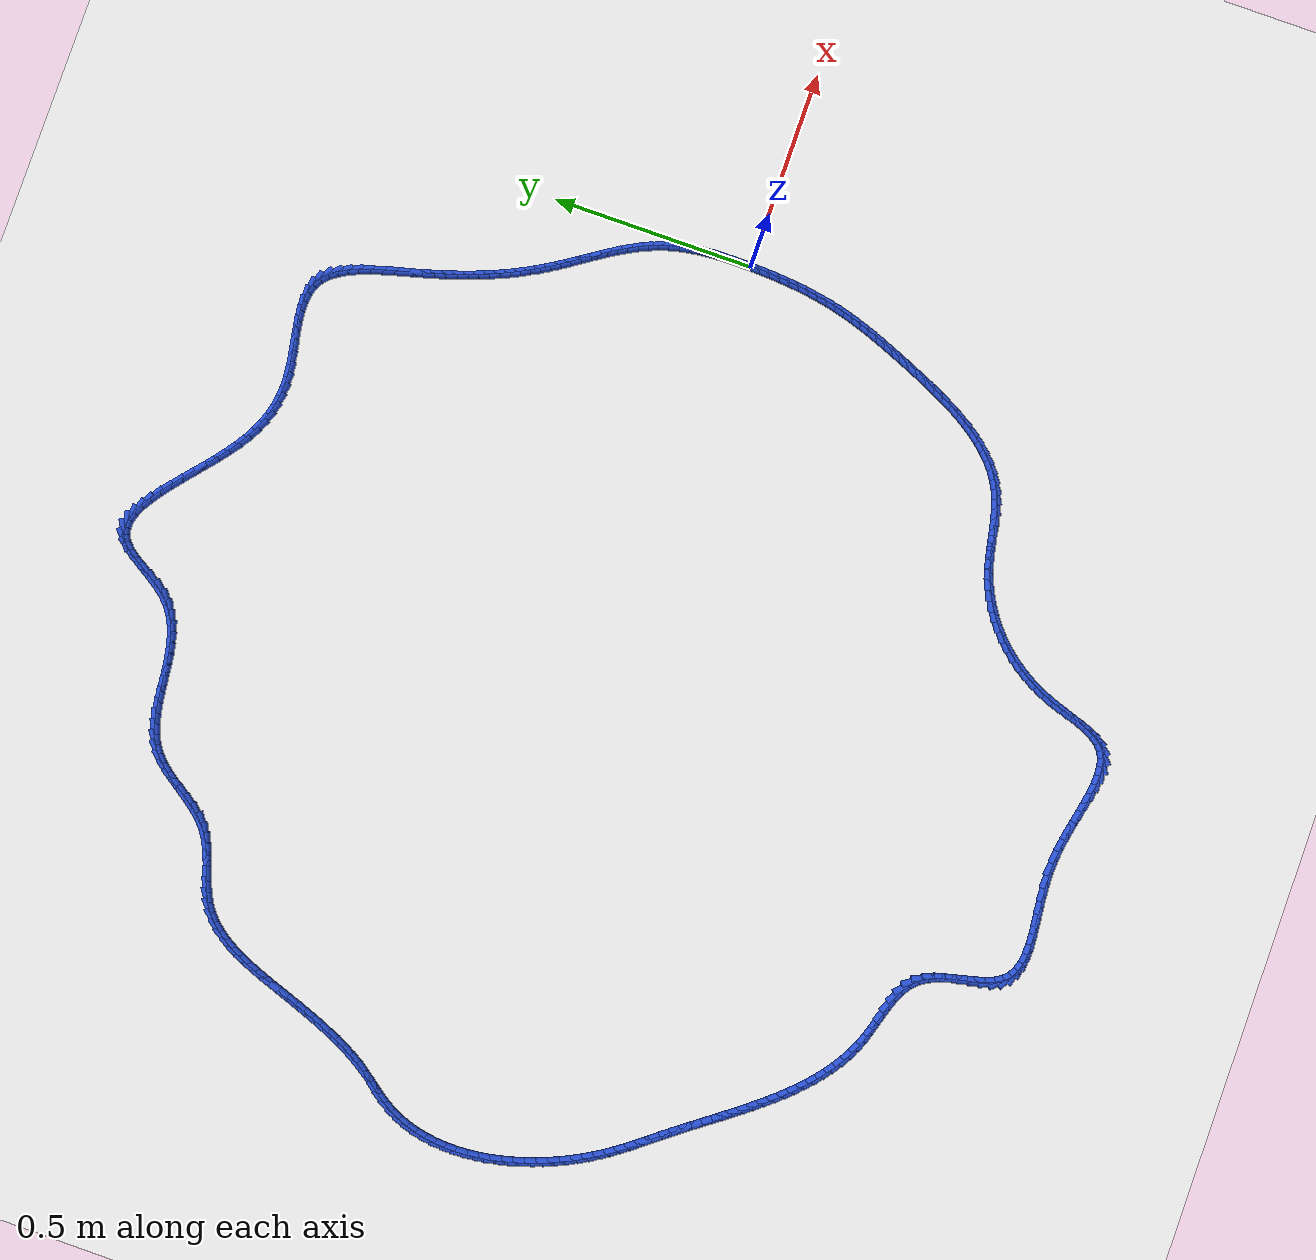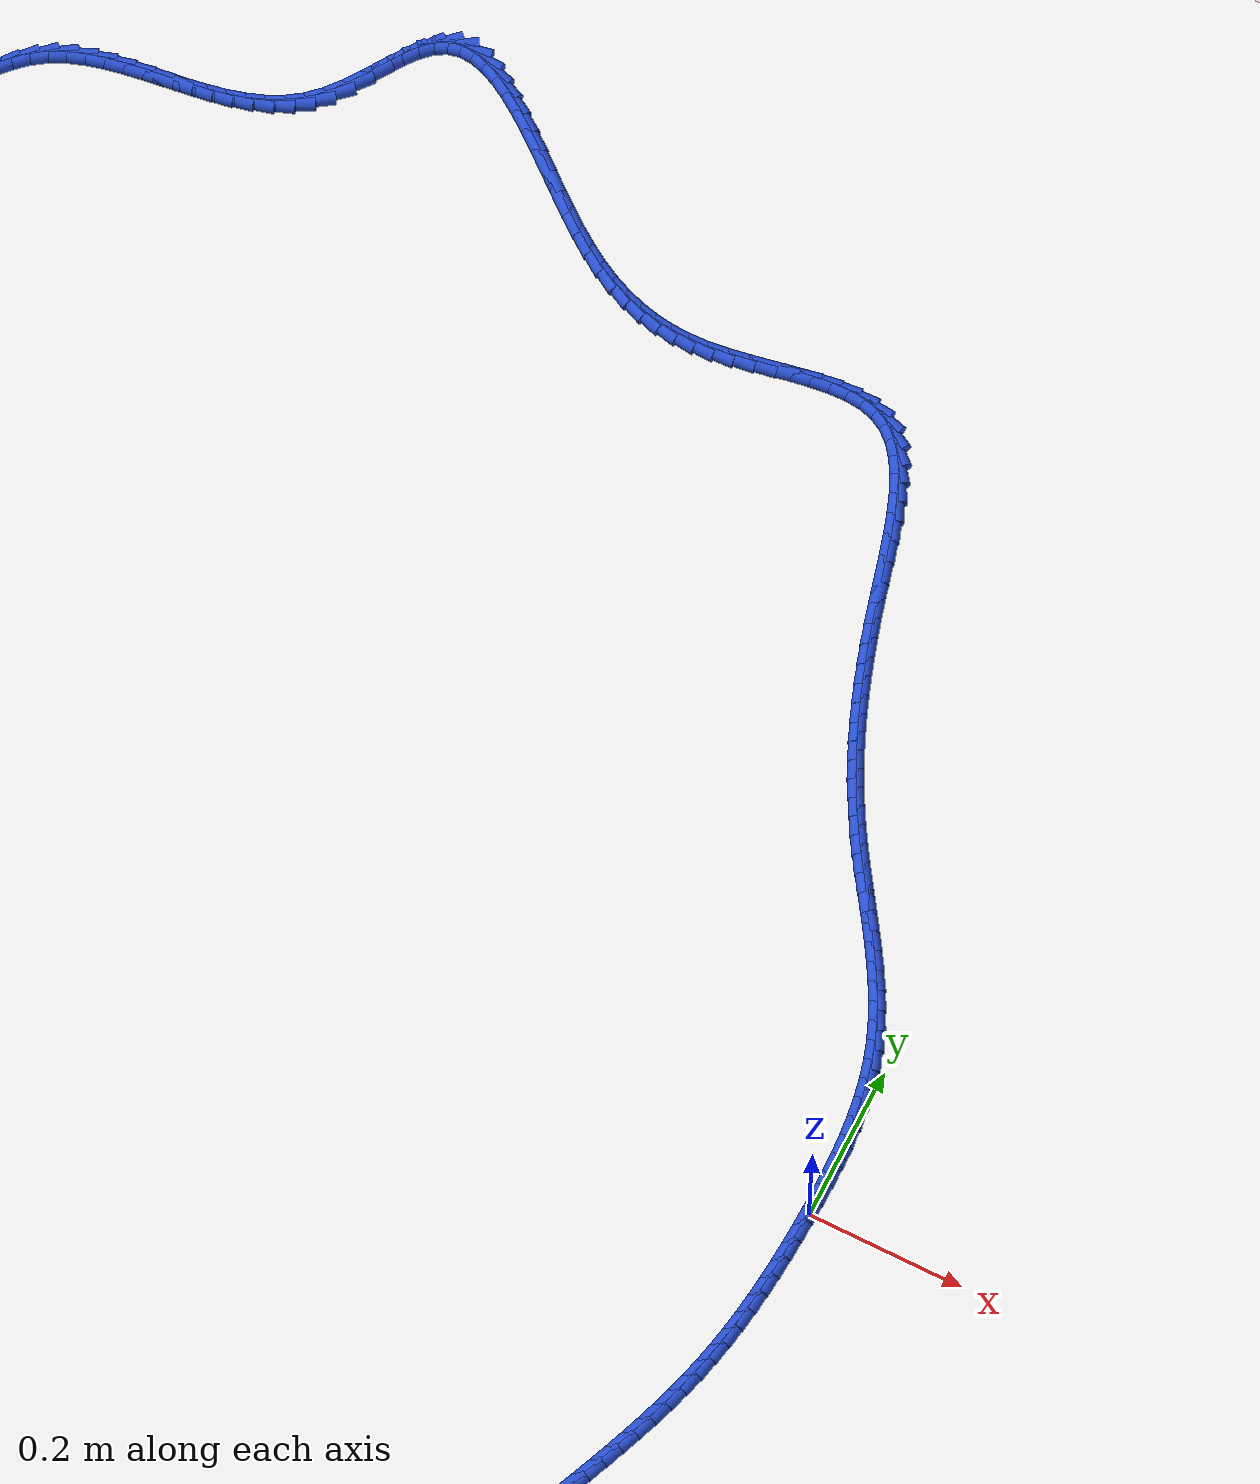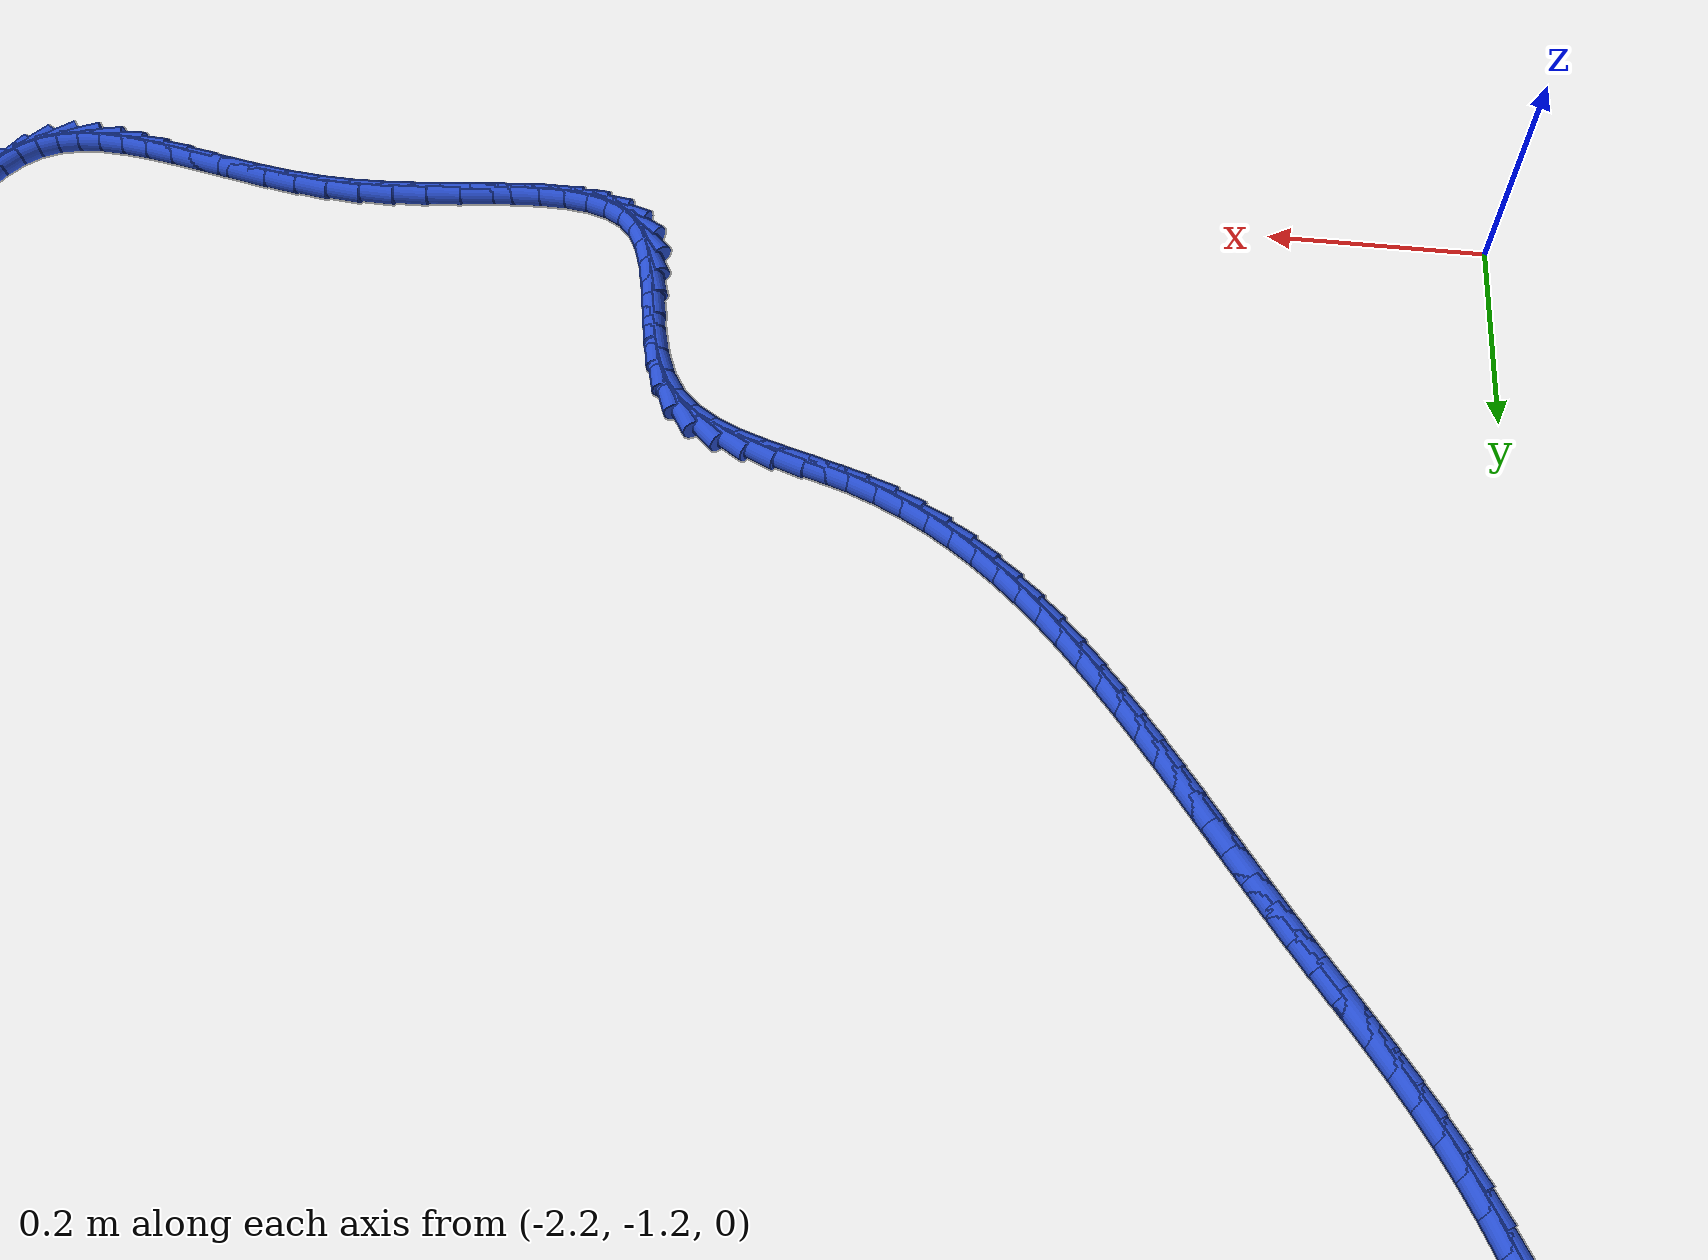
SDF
<sdf version="1.6">
 <world name="default">
  <light name="sun" type="directional">
   <pose>0 0 10 0 -0 0</pose>
   <diffuse>0.8 0.8 0.8 1</diffuse>
   <specular>0.2 0.2 0.2 1</specular>
   <attenuation>
    <range>1000</range>
    <constant>0.9</constant>
    <linear>0.01</linear>
    <quadratic>0.001</quadratic>
   </attenuation>
   <direction>-0.5 0.1 -0.9</direction>
  </light>
  <model name="ground_plane">
   <static>1</static>
   <link name="link">
    <collision name="collision">
     <geometry><plane><normal>0 0 1</normal><size>100 100</size></plane></geometry>
     <surface><friction><ode><mu>100</mu><mu2>50</mu2></ode></friction></surface>
    </collision>
    <visual name="visual">
     <cast_shadows>0</cast_shadows>
     <geometry><plane><normal>0 0 1</normal><size>100 100</size></plane></geometry>
     <material>
      <script><uri>file://media/materials/scripts/gazebo.material</uri><name>Gazebo/WhiteGlow</name></script>
     </material>
    </visual>
   </link>
  </model>
  <gravity>0 0 -9.8</gravity>
  <magnetic_field>6e-06 2.3e-05 -4.2e-05</magnetic_field>
  <atmosphere type="adiabatic"/>
  <physics name="default_physics" default="0" type="ode">
   <max_step_size>0.001</max_step_size>
   <real_time_factor>1</real_time_factor>
   <real_time_update_rate>1000</real_time_update_rate>
  </physics>
  <scene><ambient>0.4 0.4 0.4 1</ambient><background>0.7 0.7 0.7 1</background><shadows>1</shadows></scene>
  <spherical_coordinates>
   <surface_model>EARTH_WGS84</surface_model>
   <latitude_deg>0</latitude_deg>
   <longitude_deg>0</longitude_deg>
   <elevation>0</elevation>
   <heading_deg>0</heading_deg>
  </spherical_coordinates>
  <model name="line">
   <link name="link_0">
    <pose>9.324138683375338e-18 0.0 0.01 0 1.57 1.5542884025742656</pose>
    <collision name="collision">
     <geometry><cylinder><radius>0.01</radius><length>0.08</length></cylinder></geometry>
    </collision>
    <visual name="visual">
     <material>
      <script><name>Gazebo/Blue</name><uri>file://media/materials/scripts/gazebo.material</uri></script>
     </material>
     <geometry><cylinder><radius>0.01</radius><length>0.08</length></cylinder></geometry>
    </visual>
   </link>
   <link name="link_1">
    <pose>0.00042943801422285963 0.02601168983052005 0.01 0 1.57 -1.5676252205902421</pose>
    <collision name="collision">
     <geometry><cylinder><radius>0.01</radius><length>0.08</length></cylinder></geometry>
    </collision>
    <visual name="visual">
     <material>
      <script><name>Gazebo/Blue</name><uri>file://media/materials/scripts/gazebo.material</uri></script>
     </material>
     <geometry><cylinder><radius>0.01</radius><length>0.08</length></cylinder></geometry>
    </visual>
   </link>
   <link name="link_2">
    <pose>0.0003469676792073009 0.05201840586422096 0.01 0 1.57 -1.5421554651012233</pose>
    <collision name="collision">
     <geometry><cylinder><radius>0.01</radius><length>0.08</length></cylinder></geometry>
    </collision>
    <visual name="visual">
     <material>
      <script><name>Gazebo/Blue</name><uri>file://media/materials/scripts/gazebo.material</uri></script>
     </material>
     <geometry><cylinder><radius>0.01</radius><length>0.08</length></cylinder></geometry>
    </visual>
   </link>
   <link name="link_3">
    <pose>-0.0003959502156660262 0.07795040307326778 0.01 0 1.57 -1.5106883978143857</pose>
    <collision name="collision">
     <geometry><cylinder><radius>0.01</radius><length>0.08</length></cylinder></geometry>
    </collision>
    <visual name="visual">
     <material>
      <script><name>Gazebo/Blue</name><uri>file://media/materials/scripts/gazebo.material</uri></script>
     </material>
     <geometry><cylinder><radius>0.01</radius><length>0.08</length></cylinder></geometry>
    </visual>
   </link>
   <link name="link_4">
    <pose>-0.001947854881016481 0.10373793642982548 0.01 0 1.57 -1.4729825863999648</pose>
    <collision name="collision">
     <geometry><cylinder><radius>0.01</radius><length>0.08</length></cylinder></geometry>
    </collision>
    <visual name="visual">
     <material>
      <script><name>Gazebo/Blue</name><uri>file://media/materials/scripts/gazebo.material</uri></script>
     </material>
     <geometry><cylinder><radius>0.01</radius><length>0.08</length></cylinder></geometry>
    </visual>
   </link>
   <link name="link_5">
    <pose>-0.004457285527463422 0.1293112609060592 0.01 0 1.57 -1.4287935360095947</pose>
    <collision name="collision">
     <geometry><cylinder><radius>0.01</radius><length>0.08</length></cylinder></geometry>
    </collision>
    <visual name="visual">
     <material>
      <script><name>Gazebo/Blue</name><uri>file://media/materials/scripts/gazebo.material</uri></script>
     </material>
     <geometry><cylinder><radius>0.01</radius><length>0.08</length></cylinder></geometry>
    </visual>
   </link>
   <link name="link_6">
    <pose>-0.008072781365626213 0.15460063147413394 0.01 0 1.57 -1.3779177365567081</pose>
    <collision name="collision">
     <geometry><cylinder><radius>0.01</radius><length>0.08</length></cylinder></geometry>
    </collision>
    <visual name="visual">
     <material>
      <script><name>Gazebo/Blue</name><uri>file://media/materials/scripts/gazebo.material</uri></script>
     </material>
     <geometry><cylinder><radius>0.01</radius><length>0.08</length></cylinder></geometry>
    </visual>
   </link>
   <link name="link_7">
    <pose>-0.0129428816061242 0.17953630310621466 0.01 0 1.57 -1.3202508523883352</pose>
    <collision name="collision">
     <geometry><cylinder><radius>0.01</radius><length>0.08</length></cylinder></geometry>
    </collision>
    <visual name="visual">
     <material>
      <script><name>Gazebo/Blue</name><uri>file://media/materials/scripts/gazebo.material</uri></script>
     </material>
     <geometry><cylinder><radius>0.01</radius><length>0.08</length></cylinder></geometry>
    </visual>
   </link>
   <link name="link_8">
    <pose>-0.019216125459576763 0.20404853077446658 0.01 0 1.57 -1.2558921399591056</pose>
    <collision name="collision">
     <geometry><cylinder><radius>0.01</radius><length>0.08</length></cylinder></geometry>
    </collision>
    <visual name="visual">
     <material>
      <script><name>Gazebo/Blue</name><uri>file://media/materials/scripts/gazebo.material</uri></script>
     </material>
     <geometry><cylinder><radius>0.01</radius><length>0.08</length></cylinder></geometry>
    </visual>
   </link>
   <link name="link_9">
    <pose>-0.027040258992534816 0.22806784191022758 0.01 0 1.57 -1.1899303943734874</pose>
    <collision name="collision">
     <geometry><cylinder><radius>0.01</radius><length>0.08</length></cylinder></geometry>
    </collision>
    <visual name="visual">
     <material>
      <script><name>Gazebo/Blue</name><uri>file://media/materials/scripts/gazebo.material</uri></script>
     </material>
     <geometry><cylinder><radius>0.01</radius><length>0.08</length></cylinder></geometry>
    </visual>
   </link>
   <link name="link_10">
    <pose>-0.03644855814250048 0.2515640864814819 0.01 0 1.57 -1.132437126318749</pose>
    <collision name="collision">
     <geometry><cylinder><radius>0.01</radius><length>0.08</length></cylinder></geometry>
    </collision>
    <visual name="visual">
     <material>
      <script><name>Gazebo/Blue</name><uri>file://media/materials/scripts/gazebo.material</uri></script>
     </material>
     <geometry><cylinder><radius>0.01</radius><length>0.08</length></cylinder></geometry>
    </visual>
   </link>
   <link name="link_11">
    <pose>-0.04724126271522591 0.2745871665353603 0.01 0 1.57 -1.0846140605581969</pose>
    <collision name="collision">
     <geometry><cylinder><radius>0.01</radius><length>0.08</length></cylinder></geometry>
    </collision>
    <visual name="visual">
     <material>
      <script><name>Gazebo/Blue</name><uri>file://media/materials/scripts/gazebo.material</uri></script>
     </material>
     <geometry><cylinder><radius>0.01</radius><length>0.08</length></cylinder></geometry>
    </visual>
   </link>
   <link name="link_12">
    <pose>-0.05919027905459358 0.29719671716989504 0.01 0 1.57 -1.0462569999396019</pose>
    <collision name="collision">
     <geometry><cylinder><radius>0.01</radius><length>0.08</length></cylinder></geometry>
    </collision>
    <visual name="visual">
     <material>
      <script><name>Gazebo/Blue</name><uri>file://media/materials/scripts/gazebo.material</uri></script>
     </material>
     <geometry><cylinder><radius>0.01</radius><length>0.08</length></cylinder></geometry>
    </visual>
   </link>
   <link name="link_13">
    <pose>-0.07206751350448591 0.31945237348311806 0.01 0 1.57 -1.0170747300178373</pose>
    <collision name="collision">
     <geometry><cylinder><radius>0.01</radius><length>0.08</length></cylinder></geometry>
    </collision>
    <visual name="visual">
     <material>
      <script><name>Gazebo/Blue</name><uri>file://media/materials/scripts/gazebo.material</uri></script>
     </material>
     <geometry><cylinder><radius>0.01</radius><length>0.08</length></cylinder></geometry>
    </visual>
   </link>
   <link name="link_14">
    <pose>-0.08564487240878545 0.34141377057306155 0.01 0 1.57 -0.9967871219840205</pose>
    <collision name="collision">
     <geometry><cylinder><radius>0.01</radius><length>0.08</length></cylinder></geometry>
    </collision>
    <visual name="visual">
     <material>
      <script><name>Gazebo/Blue</name><uri>file://media/materials/scripts/gazebo.material</uri></script>
     </material>
     <geometry><cylinder><radius>0.01</radius><length>0.08</length></cylinder></geometry>
    </visual>
   </link>
   <link name="link_15">
    <pose>-0.09969426211137462 0.3631405435377575 0.01 0 1.57 -0.9851916437009793</pose>
    <collision name="collision">
     <geometry><cylinder><radius>0.01</radius><length>0.08</length></cylinder></geometry>
    </collision>
    <visual name="visual">
     <material>
      <script><name>Gazebo/Blue</name><uri>file://media/materials/scripts/gazebo.material</uri></script>
     </material>
     <geometry><cylinder><radius>0.01</radius><length>0.08</length></cylinder></geometry>
    </visual>
   </link>
   <link name="link_16">
    <pose>-0.11398758895613598 0.3846923274752379 0.01 0 1.57 -0.9822056207728629</pose>
    <collision name="collision">
     <geometry><cylinder><radius>0.01</radius><length>0.08</length></cylinder></geometry>
    </collision>
    <visual name="visual">
     <material>
      <script><name>Gazebo/Blue</name><uri>file://media/materials/scripts/gazebo.material</uri></script>
     </material>
     <geometry><cylinder><radius>0.01</radius><length>0.08</length></cylinder></geometry>
    </visual>
   </link>
   <link name="link_17">
    <pose>-0.12829675928695192 0.406128757483535 0.01 0 1.57 -0.9878909543283146</pose>
    <collision name="collision">
     <geometry><cylinder><radius>0.01</radius><length>0.08</length></cylinder></geometry>
    </collision>
    <visual name="visual">
     <material>
      <script><name>Gazebo/Blue</name><uri>file://media/materials/scripts/gazebo.material</uri></script>
     </material>
     <geometry><cylinder><radius>0.01</radius><length>0.08</length></cylinder></geometry>
    </visual>
   </link>
   <link name="link_18">
    <pose>-0.14239367944770492 0.4275094686606805 0.01 0 1.57 -1.002465223025756</pose>
    <collision name="collision">
     <geometry><cylinder><radius>0.01</radius><length>0.08</length></cylinder></geometry>
    </collision>
    <visual name="visual">
     <material>
      <script><name>Gazebo/Blue</name><uri>file://media/materials/scripts/gazebo.material</uri></script>
     </material>
     <geometry><cylinder><radius>0.01</radius><length>0.08</length></cylinder></geometry>
    </visual>
   </link>
   <link name="link_19">
    <pose>-0.15605025578227755 0.44889409610470676 0.01 0 1.57 -1.0260049977630974</pose>
    <collision name="collision">
     <geometry><cylinder><radius>0.01</radius><length>0.08</length></cylinder></geometry>
    </collision>
    <visual name="visual">
     <material>
      <script><name>Gazebo/Blue</name><uri>file://media/materials/scripts/gazebo.material</uri></script>
     </material>
     <geometry><cylinder><radius>0.01</radius><length>0.08</length></cylinder></geometry>
    </visual>
   </link>
   <link name="link_20">
    <pose>-0.1690470537799566 0.4703423249946574 0.01 0 1.57 -1.0538700743237543</pose>
    <collision name="collision">
     <geometry><cylinder><radius>0.01</radius><length>0.08</length></cylinder></geometry>
    </collision>
    <visual name="visual">
     <material>
      <script><name>Gazebo/Blue</name><uri>file://media/materials/scripts/gazebo.material</uri></script>
     </material>
     <geometry><cylinder><radius>0.01</radius><length>0.08</length></cylinder></geometry>
    </visual>
   </link>
   <link name="link_21">
    <pose>-0.18131067263318124 0.4919146851097357 0.01 0 1.57 -1.0817553757917213</pose>
    <collision name="collision">
     <geometry><cylinder><radius>0.01</radius><length>0.08</length></cylinder></geometry>
    </collision>
    <visual name="visual">
     <material>
      <script><name>Gazebo/Blue</name><uri>file://media/materials/scripts/gazebo.material</uri></script>
     </material>
     <geometry><cylinder><radius>0.01</radius><length>0.08</length></cylinder></geometry>
    </visual>
   </link>
   <link name="link_22">
    <pose>-0.19288919489797185 0.5136724088400216 0.01 0 1.57 -1.1092219240259398</pose>
    <collision name="collision">
     <geometry><cylinder><radius>0.01</radius><length>0.08</length></cylinder></geometry>
    </collision>
    <visual name="visual">
     <material>
      <script><name>Gazebo/Blue</name><uri>file://media/materials/scripts/gazebo.material</uri></script>
     </material>
     <geometry><cylinder><radius>0.01</radius><length>0.08</length></cylinder></geometry>
    </visual>
   </link>
   <link name="link_23">
    <pose>-0.20383440000390873 0.5356767499568241 0.01 0 1.57 -1.1359629359607926</pose>
    <collision name="collision">
     <geometry><cylinder><radius>0.01</radius><length>0.08</length></cylinder></geometry>
    </collision>
    <visual name="visual">
     <material>
      <script><name>Gazebo/Blue</name><uri>file://media/materials/scripts/gazebo.material</uri></script>
     </material>
     <geometry><cylinder><radius>0.01</radius><length>0.08</length></cylinder></geometry>
    </visual>
   </link>
   <link name="link_24">
    <pose>-0.21419806738057198 0.5579889622314522 0.01 0 1.57 -1.1616906846191994</pose>
    <collision name="collision">
     <geometry><cylinder><radius>0.01</radius><length>0.08</length></cylinder></geometry>
    </collision>
    <visual name="visual">
     <material>
      <script><name>Gazebo/Blue</name><uri>file://media/materials/scripts/gazebo.material</uri></script>
     </material>
     <geometry><cylinder><radius>0.01</radius><length>0.08</length></cylinder></geometry>
    </visual>
   </link>
   <link name="link_25">
    <pose>-0.22403197645754183 0.5806702994352146 0.01 0 1.57 -1.1861474441206268</pose>
    <collision name="collision">
     <geometry><cylinder><radius>0.01</radius><length>0.08</length></cylinder></geometry>
    </collision>
    <visual name="visual">
     <material>
      <script><name>Gazebo/Blue</name><uri>file://media/materials/scripts/gazebo.material</uri></script>
     </material>
     <geometry><cylinder><radius>0.01</radius><length>0.08</length></cylinder></geometry>
    </visual>
   </link>
   <link name="link_26">
    <pose>-0.23338790666439851 0.6037820153394203 0.01 0 1.57 -1.2091140020605664</pose>
    <collision name="collision">
     <geometry><cylinder><radius>0.01</radius><length>0.08</length></cylinder></geometry>
    </collision>
    <visual name="visual">
     <material>
      <script><name>Gazebo/Blue</name><uri>file://media/materials/scripts/gazebo.material</uri></script>
     </material>
     <geometry><cylinder><radius>0.01</radius><length>0.08</length></cylinder></geometry>
    </visual>
   </link>
   <link name="link_27">
    <pose>-0.24231763743072213 0.6273853637153779 0.01 0 1.57 -1.2304152098504588</pose>
    <collision name="collision">
     <geometry><cylinder><radius>0.01</radius><length>0.08</length></cylinder></geometry>
    </collision>
    <visual name="visual">
     <material>
      <script><name>Gazebo/Blue</name><uri>file://media/materials/scripts/gazebo.material</uri></script>
     </material>
     <geometry><cylinder><radius>0.01</radius><length>0.08</length></cylinder></geometry>
    </visual>
   </link>
   <link name="link_28">
    <pose>-0.2508729481860929 0.6515415983343966 0.01 0 1.57 -1.2499224475458777</pose>
    <collision name="collision">
     <geometry><cylinder><radius>0.01</radius><length>0.08</length></cylinder></geometry>
    </collision>
    <visual name="visual">
     <material>
      <script><name>Gazebo/Blue</name><uri>file://media/materials/scripts/gazebo.material</uri></script>
     </material>
     <geometry><cylinder><radius>0.01</radius><length>0.08</length></cylinder></geometry>
    </visual>
   </link>
   <link name="link_29">
    <pose>-0.25910561836009105 0.6763119729677851 0.01 0 1.57 -1.2675532408221235</pose>
    <collision name="collision">
     <geometry><cylinder><radius>0.01</radius><length>0.08</length></cylinder></geometry>
    </collision>
    <visual name="visual">
     <material>
      <script><name>Gazebo/Blue</name><uri>file://media/materials/scripts/gazebo.material</uri></script>
     </material>
     <geometry><cylinder><radius>0.01</radius><length>0.08</length></cylinder></geometry>
    </visual>
   </link>
   <link name="link_30">
    <pose>-0.26706742738229683 0.7017577413868525 0.01 0 1.57 -1.2832685271068334</pose>
    <collision name="collision">
     <geometry><cylinder><radius>0.01</radius><length>0.08</length></cylinder></geometry>
    </collision>
    <visual name="visual">
     <material>
      <script><name>Gazebo/Blue</name><uri>file://media/materials/scripts/gazebo.material</uri></script>
     </material>
     <geometry><cylinder><radius>0.01</radius><length>0.08</length></cylinder></geometry>
    </visual>
   </link>
   <link name="link_31">
    <pose>-0.27481015468229036 0.7279401573629074 0.01 0 1.57 -1.297068203597419</pose>
    <collision name="collision">
     <geometry><cylinder><radius>0.01</radius><length>0.08</length></cylinder></geometry>
    </collision>
    <visual name="visual">
     <material>
      <script><name>Gazebo/Blue</name><uri>file://media/materials/scripts/gazebo.material</uri></script>
     </material>
     <geometry><cylinder><radius>0.01</radius><length>0.08</length></cylinder></geometry>
    </visual>
   </link>
   <link name="link_32">
    <pose>-0.2823855796896517 0.7549204746672588 0.01 0 1.57 -1.3080062128567485</pose>
    <collision name="collision">
     <geometry><cylinder><radius>0.01</radius><length>0.08</length></cylinder></geometry>
    </collision>
    <visual name="visual">
     <material>
      <script><name>Gazebo/Blue</name><uri>file://media/materials/scripts/gazebo.material</uri></script>
     </material>
     <geometry><cylinder><radius>0.01</radius><length>0.08</length></cylinder></geometry>
    </visual>
   </link>
   <link name="link_33">
    <pose>-0.28986203081938255 0.7827128025194404 0.01 0 1.57 -1.308238558965699</pose>
    <collision name="collision">
     <geometry><cylinder><radius>0.01</radius><length>0.08</length></cylinder></geometry>
    </collision>
    <visual name="visual">
     <material>
      <script><name>Gazebo/Blue</name><uri>file://media/materials/scripts/gazebo.material</uri></script>
     </material>
     <geometry><cylinder><radius>0.01</radius><length>0.08</length></cylinder></geometry>
    </visual>
   </link>
   <link name="link_34">
    <pose>-0.29744702114476107 0.810934742548857 0.01 0 1.57 -1.2941277822955177</pose>
    <collision name="collision">
     <geometry><cylinder><radius>0.01</radius><length>0.08</length></cylinder></geometry>
    </collision>
    <visual name="visual">
     <material>
      <script><name>Gazebo/Blue</name><uri>file://media/materials/scripts/gazebo.material</uri></script>
     </material>
     <geometry><cylinder><radius>0.01</radius><length>0.08</length></cylinder></geometry>
    </visual>
   </link>
   <link name="link_35">
    <pose>-0.30541772279441165 0.8390054525010274 0.01 0 1.57 -1.2648736834470908</pose>
    <collision name="collision">
     <geometry><cylinder><radius>0.01</radius><length>0.08</length></cylinder></geometry>
    </collision>
    <visual name="visual">
     <material>
      <script><name>Gazebo/Blue</name><uri>file://media/materials/scripts/gazebo.material</uri></script>
     </material>
     <geometry><cylinder><radius>0.01</radius><length>0.08</length></cylinder></geometry>
    </visual>
   </link>
   <link name="link_36">
    <pose>-0.314051826333116 0.8663426132067444 0.01 0 1.57 -1.2181983686522753</pose>
    <collision name="collision">
     <geometry><cylinder><radius>0.01</radius><length>0.08</length></cylinder></geometry>
    </collision>
    <visual name="visual">
     <material>
      <script><name>Gazebo/Blue</name><uri>file://media/materials/scripts/gazebo.material</uri></script>
     </material>
     <geometry><cylinder><radius>0.01</radius><length>0.08</length></cylinder></geometry>
    </visual>
   </link>
   <link name="link_37">
    <pose>-0.323627022325656 0.8923639054968012 0.01 0 1.57 -1.150061695919164</pose>
    <collision name="collision">
     <geometry><cylinder><radius>0.01</radius><length>0.08</length></cylinder></geometry>
    </collision>
    <visual name="visual">
     <material>
      <script><name>Gazebo/Blue</name><uri>file://media/materials/scripts/gazebo.material</uri></script>
     </material>
     <geometry><cylinder><radius>0.01</radius><length>0.08</length></cylinder></geometry>
    </visual>
   </link>
   <link name="link_38">
    <pose>-0.334421001336813 0.916487010201991 0.01 0 1.57 -1.0543274893828696</pose>
    <collision name="collision">
     <geometry><cylinder><radius>0.01</radius><length>0.08</length></cylinder></geometry>
    </collision>
    <visual name="visual">
     <material>
      <script><name>Gazebo/Blue</name><uri>file://media/materials/scripts/gazebo.material</uri></script>
     </material>
     <geometry><cylinder><radius>0.01</radius><length>0.08</length></cylinder></geometry>
    </visual>
   </link>
   <link name="link_39">
    <pose>-0.346711453931369 0.9381296081531065 0.01 0 1.57 -0.9228395115434743</pose>
    <collision name="collision">
     <geometry><cylinder><radius>0.01</radius><length>0.08</length></cylinder></geometry>
    </collision>
    <visual name="visual">
     <material>
      <script><name>Gazebo/Blue</name><uri>file://media/materials/scripts/gazebo.material</uri></script>
     </material>
     <geometry><cylinder><radius>0.01</radius><length>0.08</length></cylinder></geometry>
    </visual>
   </link>
   <link name="link_40">
    <pose>-0.3607760706741054 0.9567093801809405 0.01 0 1.57 -0.7473552476953437</pose>
    <collision name="collision">
     <geometry><cylinder><radius>0.01</radius><length>0.08</length></cylinder></geometry>
    </collision>
    <visual name="visual">
     <material>
      <script><name>Gazebo/Blue</name><uri>file://media/materials/scripts/gazebo.material</uri></script>
     </material>
     <geometry><cylinder><radius>0.01</radius><length>0.08</length></cylinder></geometry>
    </visual>
   </link>
   <link name="link_41">
    <pose>-0.3768925421298043 0.9716440071162866 0.01 0 1.57 -0.526071035308907</pose>
    <collision name="collision">
     <geometry><cylinder><radius>0.01</radius><length>0.08</length></cylinder></geometry>
    </collision>
    <visual name="visual">
     <material>
      <script><name>Gazebo/Blue</name><uri>file://media/materials/scripts/gazebo.material</uri></script>
     </material>
     <geometry><cylinder><radius>0.01</radius><length>0.08</length></cylinder></geometry>
    </visual>
   </link>
   <link name="link_42">
    <pose>-0.39533720538927836 0.9823539254431387 0.01 0 1.57 -0.29382816515059773</pose>
    <collision name="collision">
     <geometry><cylinder><radius>0.01</radius><length>0.08</length></cylinder></geometry>
    </collision>
    <visual name="visual">
     <material>
      <script><name>Gazebo/Blue</name><uri>file://media/materials/scripts/gazebo.material</uri></script>
     </material>
     <geometry><cylinder><radius>0.01</radius><length>0.08</length></cylinder></geometry>
    </visual>
   </link>
   <link name="link_43">
    <pose>-0.4161881748228289 0.9886631502048843 0.01 0 1.57 -0.11106326772097562</pose>
    <collision name="collision">
     <geometry><cylinder><radius>0.01</radius><length>0.08</length></cylinder></geometry>
    </collision>
    <visual name="visual">
     <material>
      <script><name>Gazebo/Blue</name><uri>file://media/materials/scripts/gazebo.material</uri></script>
     </material>
     <geometry><cylinder><radius>0.01</radius><length>0.08</length></cylinder></geometry>
    </visual>
   </link>
   <link name="link_44">
    <pose>-0.43911850567519245 0.9912203908994147 0.01 0 1.57 0.01807580407839804</pose>
    <collision name="collision">
     <geometry><cylinder><radius>0.01</radius><length>0.08</length></cylinder></geometry>
    </collision>
    <visual name="visual">
     <material>
      <script><name>Gazebo/Blue</name><uri>file://media/materials/scripts/gazebo.material</uri></script>
     </material>
     <geometry><cylinder><radius>0.01</radius><length>0.08</length></cylinder></geometry>
    </visual>
   </link>
   <link name="link_45">
    <pose>-0.46375178374650516 0.9907750760902 0.01 0 1.57 0.10357492263722988</pose>
    <collision name="collision">
     <geometry><cylinder><radius>0.01</radius><length>0.08</length></cylinder></geometry>
    </collision>
    <visual name="visual">
     <material>
      <script><name>Gazebo/Blue</name><uri>file://media/materials/scripts/gazebo.material</uri></script>
     </material>
     <geometry><cylinder><radius>0.01</radius><length>0.08</length></cylinder></geometry>
    </visual>
   </link>
   <link name="link_46">
    <pose>-0.4897115948369035 0.9880766343407078 0.01 0 1.57 0.15490473094127422</pose>
    <collision name="collision">
     <geometry><cylinder><radius>0.01</radius><length>0.08</length></cylinder></geometry>
    </collision>
    <visual name="visual">
     <material>
      <script><name>Gazebo/Blue</name><uri>file://media/materials/scripts/gazebo.material</uri></script>
     </material>
     <geometry><cylinder><radius>0.01</radius><length>0.08</length></cylinder></geometry>
    </visual>
   </link>
   <link name="link_47">
    <pose>-0.516621524746523 0.9838744942144068 0.01 0 1.57 0.17842264621961873</pose>
    <collision name="collision">
     <geometry><cylinder><radius>0.01</radius><length>0.08</length></cylinder></geometry>
    </collision>
    <visual name="visual">
     <material>
      <script><name>Gazebo/Blue</name><uri>file://media/materials/scripts/gazebo.material</uri></script>
     </material>
     <geometry><cylinder><radius>0.01</radius><length>0.08</length></cylinder></geometry>
    </visual>
   </link>
   <link name="link_48">
    <pose>-0.5441051592755005 0.9789180842747656 0.01 0 1.57 0.1773469686632341</pose>
    <collision name="collision">
     <geometry><cylinder><radius>0.01</radius><length>0.08</length></cylinder></geometry>
    </collision>
    <visual name="visual">
     <material>
      <script><name>Gazebo/Blue</name><uri>file://media/materials/scripts/gazebo.material</uri></script>
     </material>
     <geometry><cylinder><radius>0.01</radius><length>0.08</length></cylinder></geometry>
    </visual>
   </link>
   <link name="link_49">
    <pose>-0.5717860842239714 0.9739568330852524 0.01 0 1.57 0.1521384157351567</pose>
    <collision name="collision">
     <geometry><cylinder><radius>0.01</radius><length>0.08</length></cylinder></geometry>
    </collision>
    <visual name="visual">
     <material>
      <script><name>Gazebo/Blue</name><uri>file://media/materials/scripts/gazebo.material</uri></script>
     </material>
     <geometry><cylinder><radius>0.01</radius><length>0.08</length></cylinder></geometry>
    </visual>
   </link>
   <link name="link_50">
    <pose>-0.5992878853920727 0.9697401692093358 0.01 0 1.57 0.10069815967747947</pose>
    <collision name="collision">
     <geometry><cylinder><radius>0.01</radius><length>0.08</length></cylinder></geometry>
    </collision>
    <visual name="visual">
     <material>
      <script><name>Gazebo/Blue</name><uri>file://media/materials/scripts/gazebo.material</uri></script>
     </material>
     <geometry><cylinder><radius>0.01</radius><length>0.08</length></cylinder></geometry>
    </visual>
   </link>
   <link name="link_51">
    <pose>-0.62623414857994 0.9670175212104848 0.01 0 1.57 0.022690435234517782</pose>
    <collision name="collision">
     <geometry><cylinder><radius>0.01</radius><length>0.08</length></cylinder></geometry>
    </collision>
    <visual name="visual">
     <material>
      <script><name>Gazebo/Blue</name><uri>file://media/materials/scripts/gazebo.material</uri></script>
     </material>
     <geometry><cylinder><radius>0.01</radius><length>0.08</length></cylinder></geometry>
    </visual>
   </link>
   <link name="link_52">
    <pose>-0.6523306386119622 0.9664252788502613 0.01 0 1.57 -0.06630912293535449</pose>
    <collision name="collision">
     <geometry><cylinder><radius>0.01</radius><length>0.08</length></cylinder></geometry>
    </collision>
    <visual name="visual">
     <material>
      <script><name>Gazebo/Blue</name><uri>file://media/materials/scripts/gazebo.material</uri></script>
     </material>
     <geometry><cylinder><radius>0.01</radius><length>0.08</length></cylinder></geometry>
    </visual>
   </link>
   <link name="link_53">
    <pose>-0.6776420477516023 0.9681061204102857 0.01 0 1.57 -0.15911380259047758</pose>
    <collision name="collision">
     <geometry><cylinder><radius>0.01</radius><length>0.08</length></cylinder></geometry>
    </collision>
    <visual name="visual">
     <material>
      <script><name>Gazebo/Blue</name><uri>file://media/materials/scripts/gazebo.material</uri></script>
     </material>
     <geometry><cylinder><radius>0.01</radius><length>0.08</length></cylinder></geometry>
    </visual>
   </link>
   <link name="link_54">
    <pose>-0.7023310344374831 0.9720679698456581 0.01 0 1.57 -0.25247978371280994</pose>
    <collision name="collision">
     <geometry><cylinder><radius>0.01</radius><length>0.08</length></cylinder></geometry>
    </collision>
    <visual name="visual">
     <material>
      <script><name>Gazebo/Blue</name><uri>file://media/materials/scripts/gazebo.material</uri></script>
     </material>
     <geometry><cylinder><radius>0.01</radius><length>0.08</length></cylinder></geometry>
    </visual>
   </link>
   <link name="link_55">
    <pose>-0.7265602593668018 0.9783187480047648 0.01 0 1.57 -0.343040269392239</pose>
    <collision name="collision">
     <geometry><cylinder><radius>0.01</radius><length>0.08</length></cylinder></geometry>
    </collision>
    <visual name="visual">
     <material>
      <script><name>Gazebo/Blue</name><uri>file://media/materials/scripts/gazebo.material</uri></script>
     </material>
     <geometry><cylinder><radius>0.01</radius><length>0.08</length></cylinder></geometry>
    </visual>
   </link>
   <link name="link_56">
    <pose>-0.7504923832367556 0.9868663757359928 0.01 0 1.57 -0.427855078939923</pose>
    <collision name="collision">
     <geometry><cylinder><radius>0.01</radius><length>0.08</length></cylinder></geometry>
    </collision>
    <visual name="visual">
     <material>
      <script><name>Gazebo/Blue</name><uri>file://media/materials/scripts/gazebo.material</uri></script>
     </material>
     <geometry><cylinder><radius>0.01</radius><length>0.08</length></cylinder></geometry>
    </visual>
   </link>
   <link name="link_57">
    <pose>-0.7742900667445427 0.9977187738877286 0.01 0 1.57 -0.5048016494929995</pose>
    <collision name="collision">
     <geometry><cylinder><radius>0.01</radius><length>0.08</length></cylinder></geometry>
    </collision>
    <visual name="visual">
     <material>
      <script><name>Gazebo/Blue</name><uri>file://media/materials/scripts/gazebo.material</uri></script>
     </material>
     <geometry><cylinder><radius>0.01</radius><length>0.08</length></cylinder></geometry>
    </visual>
   </link>
   <link name="link_58">
    <pose>-0.7981159705873603 1.010883863308359 0.01 0 1.57 -0.5726924202510537</pose>
    <collision name="collision">
     <geometry><cylinder><radius>0.01</radius><length>0.08</length></cylinder></geometry>
    </collision>
    <visual name="visual">
     <material>
      <script><name>Gazebo/Blue</name><uri>file://media/materials/scripts/gazebo.material</uri></script>
     </material>
     <geometry><cylinder><radius>0.01</radius><length>0.08</length></cylinder></geometry>
    </visual>
   </link>
   <link name="link_59">
    <pose>-0.8221325474726502 1.026369120536926 0.01 0 1.57 -0.628336960581758</pose>
    <collision name="collision">
     <geometry><cylinder><radius>0.01</radius><length>0.08</length></cylinder></geometry>
    </collision>
    <visual name="visual">
     <material>
      <script><name>Gazebo/Blue</name><uri>file://media/materials/scripts/gazebo.material</uri></script>
     </material>
     <geometry><cylinder><radius>0.01</radius><length>0.08</length></cylinder></geometry>
    </visual>
   </link>
   <link name="link_60">
    <pose>-0.8464266349061412 1.044020492326438 0.01 0 1.57 -0.6668645390080629</pose>
    <collision name="collision">
     <geometry><cylinder><radius>0.01</radius><length>0.08</length></cylinder></geometry>
    </collision>
    <visual name="visual">
     <material>
      <script><name>Gazebo/Blue</name><uri>file://media/materials/scripts/gazebo.material</uri></script>
     </material>
     <geometry><cylinder><radius>0.01</radius><length>0.08</length></cylinder></geometry>
    </visual>
   </link>
   <link name="link_61">
    <pose>-0.870897369256108 1.0632829567902065 0.01 0 1.57 -0.6905305884854358</pose>
    <collision name="collision">
     <geometry><cylinder><radius>0.01</radius><length>0.08</length></cylinder></geometry>
    </collision>
    <visual name="visual">
     <material>
      <script><name>Gazebo/Blue</name><uri>file://media/materials/scripts/gazebo.material</uri></script>
     </material>
     <geometry><cylinder><radius>0.01</radius><length>0.08</length></cylinder></geometry>
    </visual>
   </link>
   <link name="link_62">
    <pose>-0.895415258543993 1.0835403359428561 0.01 0 1.57 -0.7012993268502032</pose>
    <collision name="collision">
     <geometry><cylinder><radius>0.01</radius><length>0.08</length></cylinder></geometry>
    </collision>
    <visual name="visual">
     <material>
      <script><name>Gazebo/Blue</name><uri>file://media/materials/scripts/gazebo.material</uri></script>
     </material>
     <geometry><cylinder><radius>0.01</radius><length>0.08</length></cylinder></geometry>
    </visual>
   </link>
   <link name="link_63">
    <pose>-0.9198508107912399 1.1041764517990122 0.01 0 1.57 -0.699886825276258</pose>
    <collision name="collision">
     <geometry><cylinder><radius>0.01</radius><length>0.08</length></cylinder></geometry>
    </collision>
    <visual name="visual">
     <material>
      <script><name>Gazebo/Blue</name><uri>file://media/materials/scripts/gazebo.material</uri></script>
     </material>
     <geometry><cylinder><radius>0.01</radius><length>0.08</length></cylinder></geometry>
    </visual>
   </link>
   <link name="link_64">
    <pose>-0.9440745340192912 1.124575126373299 0.01 0 1.57 -0.6858525999099303</pose>
    <collision name="collision">
     <geometry><cylinder><radius>0.01</radius><length>0.08</length></cylinder></geometry>
    </collision>
    <visual name="visual">
     <material>
      <script><name>Gazebo/Blue</name><uri>file://media/materials/scripts/gazebo.material</uri></script>
     </material>
     <geometry><cylinder><radius>0.01</radius><length>0.08</length></cylinder></geometry>
    </visual>
   </link>
   <link name="link_65">
    <pose>-0.9679569362495898 1.144120181680341 0.01 0 1.57 -0.6574735184225644</pose>
    <collision name="collision">
     <geometry><cylinder><radius>0.01</radius><length>0.08</length></cylinder></geometry>
    </collision>
    <visual name="visual">
     <material>
      <script><name>Gazebo/Blue</name><uri>file://media/materials/scripts/gazebo.material</uri></script>
     </material>
     <geometry><cylinder><radius>0.01</radius><length>0.08</length></cylinder></geometry>
    </visual>
   </link>
   <link name="link_66">
    <pose>-0.9913685255035795 1.1621954397347647 0.01 0 1.57 -0.6113548298505201</pose>
    <collision name="collision">
     <geometry><cylinder><radius>0.01</radius><length>0.08</length></cylinder></geometry>
    </collision>
    <visual name="visual">
     <material>
      <script><name>Gazebo/Blue</name><uri>file://media/materials/scripts/gazebo.material</uri></script>
     </material>
     <geometry><cylinder><radius>0.01</radius><length>0.08</length></cylinder></geometry>
    </visual>
   </link>
   <link name="link_67">
    <pose>-1.0141798098027022 1.1781847225511934 0.01 0 1.57 -0.5416917918737421</pose>
    <collision name="collision">
     <geometry><cylinder><radius>0.01</radius><length>0.08</length></cylinder></geometry>
    </collision>
    <visual name="visual">
     <material>
      <script><name>Gazebo/Blue</name><uri>file://media/materials/scripts/gazebo.material</uri></script>
     </material>
     <geometry><cylinder><radius>0.01</radius><length>0.08</length></cylinder></geometry>
    </visual>
   </link>
   <link name="link_68">
    <pose>-1.0362612971684018 1.1914718521442524 0.01 0 1.57 -0.4391433872743035</pose>
    <collision name="collision">
     <geometry><cylinder><radius>0.01</radius><length>0.08</length></cylinder></geometry>
    </collision>
    <visual name="visual">
     <material>
      <script><name>Gazebo/Blue</name><uri>file://media/materials/scripts/gazebo.material</uri></script>
     </material>
     <geometry><cylinder><radius>0.01</radius><length>0.08</length></cylinder></geometry>
    </visual>
   </link>
   <link name="link_69">
    <pose>-1.0574834956221202 1.2014406505285662 0.01 0 1.57 -0.28983564918691107</pose>
    <collision name="collision">
     <geometry><cylinder><radius>0.01</radius><length>0.08</length></cylinder></geometry>
    </collision>
    <visual name="visual">
     <material>
      <script><name>Gazebo/Blue</name><uri>file://media/materials/scripts/gazebo.material</uri></script>
     </material>
     <geometry><cylinder><radius>0.01</radius><length>0.08</length></cylinder></geometry>
    </visual>
   </link>
   <link name="link_70">
    <pose>-1.0777169131853017 1.2074749397187605 0.01 0 1.57 -0.07745867055720179</pose>
    <collision name="collision">
     <geometry><cylinder><radius>0.01</radius><length>0.08</length></cylinder></geometry>
    </collision>
    <visual name="visual">
     <material>
      <script><name>Gazebo/Blue</name><uri>file://media/materials/scripts/gazebo.material</uri></script>
     </material>
     <geometry><cylinder><radius>0.01</radius><length>0.08</length></cylinder></geometry>
    </visual>
   </link>
   <link name="link_71">
    <pose>-1.0968320578793884 1.2089585417294595 0.01 0 1.57 0.20329674877784998</pose>
    <collision name="collision">
     <geometry><cylinder><radius>0.01</radius><length>0.08</length></cylinder></geometry>
    </collision>
    <visual name="visual">
     <material>
      <script><name>Gazebo/Blue</name><uri>file://media/materials/scripts/gazebo.material</uri></script>
     </material>
     <geometry><cylinder><radius>0.01</radius><length>0.08</length></cylinder></geometry>
    </visual>
   </link>
   <link name="link_72">
    <pose>-1.1146994377258237 1.2052752785752883 0.01 0 1.57 0.5207765552972224</pose>
    <collision name="collision">
     <geometry><cylinder><radius>0.01</radius><length>0.08</length></cylinder></geometry>
    </collision>
    <visual name="visual">
     <material>
      <script><name>Gazebo/Blue</name><uri>file://media/materials/scripts/gazebo.material</uri></script>
     </material>
     <geometry><cylinder><radius>0.01</radius><length>0.08</length></cylinder></geometry>
    </visual>
   </link>
   <link name="link_73">
    <pose>-1.1311916424319997 1.195815458470249 0.01 0 1.57 0.7834575162184493</pose>
    <collision name="collision">
     <geometry><cylinder><radius>0.01</radius><length>0.08</length></cylinder></geometry>
    </collision>
    <visual name="visual">
     <material>
      <script><name>Gazebo/Blue</name><uri>file://media/materials/scripts/gazebo.material</uri></script>
     </material>
     <geometry><cylinder><radius>0.01</radius><length>0.08</length></cylinder></geometry>
    </visual>
   </link>
   <link name="link_74">
    <pose>-1.1464036653279823 1.1806623636283209 0.01 0 1.57 0.932386171864083</pose>
    <collision name="collision">
     <geometry><cylinder><radius>0.01</radius><length>0.08</length></cylinder></geometry>
    </collision>
    <visual name="visual">
     <material>
      <script><name>Gazebo/Blue</name><uri>file://media/materials/scripts/gazebo.material</uri></script>
     </material>
     <geometry><cylinder><radius>0.01</radius><length>0.08</length></cylinder></geometry>
    </visual>
   </link>
   <link name="link_75">
    <pose>-1.160847428183159 1.1611983583774643 0.01 0 1.57 1.0016892071600865</pose>
    <collision name="collision">
     <geometry><cylinder><radius>0.01</radius><length>0.08</length></cylinder></geometry>
    </collision>
    <visual name="visual">
     <material>
      <script><name>Gazebo/Blue</name><uri>file://media/materials/scripts/gazebo.material</uri></script>
     </material>
     <geometry><cylinder><radius>0.01</radius><length>0.08</length></cylinder></geometry>
    </visual>
   </link>
   <link name="link_76">
    <pose>-1.1750807244399772 1.138948735818045 0.01 0 1.57 1.0156636988688674</pose>
    <collision name="collision">
     <geometry><cylinder><radius>0.01</radius><length>0.08</length></cylinder></geometry>
    </collision>
    <visual name="visual">
     <material>
      <script><name>Gazebo/Blue</name><uri>file://media/materials/scripts/gazebo.material</uri></script>
     </material>
     <geometry><cylinder><radius>0.01</radius><length>0.08</length></cylinder></geometry>
    </visual>
   </link>
   <link name="link_77">
    <pose>-1.1896613475408875 1.1154387890504303 0.01 0 1.57 0.9831186835354228</pose>
    <collision name="collision">
     <geometry><cylinder><radius>0.01</radius><length>0.08</length></cylinder></geometry>
    </collision>
    <visual name="visual">
     <material>
      <script><name>Gazebo/Blue</name><uri>file://media/materials/scripts/gazebo.material</uri></script>
     </material>
     <geometry><cylinder><radius>0.01</radius><length>0.08</length></cylinder></geometry>
    </visual>
   </link>
   <link name="link_78">
    <pose>-1.2051470909283384 1.0921938111749847 0.01 0 1.57 0.9021990723939273</pose>
    <collision name="collision">
     <geometry><cylinder><radius>0.01</radius><length>0.08</length></cylinder></geometry>
    </collision>
    <visual name="visual">
     <material>
      <script><name>Gazebo/Blue</name><uri>file://media/materials/scripts/gazebo.material</uri></script>
     </material>
     <geometry><cylinder><radius>0.01</radius><length>0.08</length></cylinder></geometry>
    </visual>
   </link>
   <link name="link_79">
    <pose>-1.2220957480447778 1.0707390952920761 0.01 0 1.57 0.7653752254384857</pose>
    <collision name="collision">
     <geometry><cylinder><radius>0.01</radius><length>0.08</length></cylinder></geometry>
    </collision>
    <visual name="visual">
     <material>
      <script><name>Gazebo/Blue</name><uri>file://media/materials/scripts/gazebo.material</uri></script>
     </material>
     <geometry><cylinder><radius>0.01</radius><length>0.08</length></cylinder></geometry>
    </visual>
   </link>
   <link name="link_80">
    <pose>-1.2410393216244726 1.0525393396941023 0.01 0 1.57 0.6050468437623263</pose>
    <collision name="collision">
     <geometry><cylinder><radius>0.01</radius><length>0.08</length></cylinder></geometry>
    </collision>
    <visual name="visual">
     <material>
      <script><name>Gazebo/Blue</name><uri>file://media/materials/scripts/gazebo.material</uri></script>
     </material>
     <geometry><cylinder><radius>0.01</radius><length>0.08</length></cylinder></geometry>
    </visual>
   </link>
   <link name="link_81">
    <pose>-1.2620598767846136 1.0380021222830187 0.01 0 1.57 0.46248123983199807</pose>
    <collision name="collision">
     <geometry><cylinder><radius>0.01</radius><length>0.08</length></cylinder></geometry>
    </collision>
    <visual name="visual">
     <material>
      <script><name>Gazebo/Blue</name><uri>file://media/materials/scripts/gazebo.material</uri></script>
     </material>
     <geometry><cylinder><radius>0.01</radius><length>0.08</length></cylinder></geometry>
    </visual>
   </link>
   <link name="link_82">
    <pose>-1.2848571349775566 1.02663671135315 0.01 0 1.57 0.3447802142320116</pose>
    <collision name="collision">
     <geometry><cylinder><radius>0.01</radius><length>0.08</length></cylinder></geometry>
    </collision>
    <visual name="visual">
     <material>
      <script><name>Gazebo/Blue</name><uri>file://media/materials/scripts/gazebo.material</uri></script>
     </material>
     <geometry><cylinder><radius>0.01</radius><length>0.08</length></cylinder></geometry>
    </visual>
   </link>
   <link name="link_83">
    <pose>-1.3091186581411147 1.017923806636705 0.01 0 1.57 0.2533441621984295</pose>
    <collision name="collision">
     <geometry><cylinder><radius>0.01</radius><length>0.08</length></cylinder></geometry>
    </collision>
    <visual name="visual">
     <material>
      <script><name>Gazebo/Blue</name><uri>file://media/materials/scripts/gazebo.material</uri></script>
     </material>
     <geometry><cylinder><radius>0.01</radius><length>0.08</length></cylinder></geometry>
    </visual>
   </link>
   <link name="link_84">
    <pose>-1.3345320082130996 1.0113441078658896 0.01 0 1.57 0.18694465350337885</pose>
    <collision name="collision">
     <geometry><cylinder><radius>0.01</radius><length>0.08</length></cylinder></geometry>
    </collision>
    <visual name="visual">
     <material>
      <script><name>Gazebo/Blue</name><uri>file://media/materials/scripts/gazebo.material</uri></script>
     </material>
     <geometry><cylinder><radius>0.01</radius><length>0.08</length></cylinder></geometry>
    </visual>
   </link>
   <link name="link_85">
    <pose>-1.360784747131323 1.0063783147729102 0.01 0 1.57 0.1435623732843166</pose>
    <collision name="collision">
     <geometry><cylinder><radius>0.01</radius><length>0.08</length></cylinder></geometry>
    </collision>
    <visual name="visual">
     <material>
      <script><name>Gazebo/Blue</name><uri>file://media/materials/scripts/gazebo.material</uri></script>
     </material>
     <geometry><cylinder><radius>0.01</radius><length>0.08</length></cylinder></geometry>
    </visual>
   </link>
   <link name="link_86">
    <pose>-1.387564436833598 1.0025071270899741 0.01 0 1.57 0.12149459859273143</pose>
    <collision name="collision">
     <geometry><cylinder><radius>0.01</radius><length>0.08</length></cylinder></geometry>
    </collision>
    <visual name="visual">
     <material>
      <script><name>Gazebo/Blue</name><uri>file://media/materials/scripts/gazebo.material</uri></script>
     </material>
     <geometry><cylinder><radius>0.01</radius><length>0.08</length></cylinder></geometry>
    </visual>
   </link>
   <link name="link_87">
    <pose>-1.4145586392577363 0.9992112445492884 0.01 0 1.57 0.11988061695273057</pose>
    <collision name="collision">
     <geometry><cylinder><radius>0.01</radius><length>0.08</length></cylinder></geometry>
    </collision>
    <visual name="visual">
     <material>
      <script><name>Gazebo/Blue</name><uri>file://media/materials/scripts/gazebo.material</uri></script>
     </material>
     <geometry><cylinder><radius>0.01</radius><length>0.08</length></cylinder></geometry>
    </visual>
   </link>
   <link name="link_88">
    <pose>-1.44145491634155 0.9959713668830605 0.01 0 1.57 0.1389161610265466</pose>
    <collision name="collision">
     <geometry><cylinder><radius>0.01</radius><length>0.08</length></cylinder></geometry>
    </collision>
    <visual name="visual">
     <material>
      <script><name>Gazebo/Blue</name><uri>file://media/materials/scripts/gazebo.material</uri></script>
     </material>
     <geometry><cylinder><radius>0.01</radius><length>0.08</length></cylinder></geometry>
    </visual>
   </link>
   <link name="link_89">
    <pose>-1.4679408300228518 0.9922681938234967 0.01 0 1.57 0.1799123574051523</pose>
    <collision name="collision">
     <geometry><cylinder><radius>0.01</radius><length>0.08</length></cylinder></geometry>
    </collision>
    <visual name="visual">
     <material>
      <script><name>Gazebo/Blue</name><uri>file://media/materials/scripts/gazebo.material</uri></script>
     </material>
     <geometry><cylinder><radius>0.01</radius><length>0.08</length></cylinder></geometry>
    </visual>
   </link>
   <link name="link_90">
    <pose>-1.4937039422394525 0.9875824251028037 0.01 0 1.57 0.2451954670421788</pose>
    <collision name="collision">
     <geometry><cylinder><radius>0.01</radius><length>0.08</length></cylinder></geometry>
    </collision>
    <visual name="visual">
     <material>
      <script><name>Gazebo/Blue</name><uri>file://media/materials/scripts/gazebo.material</uri></script>
     </material>
     <geometry><cylinder><radius>0.01</radius><length>0.08</length></cylinder></geometry>
    </visual>
   </link>
   <link name="link_91">
    <pose>-1.518431814929166 0.9813947604531889 0.01 0 1.57 0.3376572694538913</pose>
    <collision name="collision">
     <geometry><cylinder><radius>0.01</radius><length>0.08</length></cylinder></geometry>
    </collision>
    <visual name="visual">
     <material>
      <script><name>Gazebo/Blue</name><uri>file://media/materials/scripts/gazebo.material</uri></script>
     </material>
     <geometry><cylinder><radius>0.01</radius><length>0.08</length></cylinder></geometry>
    </visual>
   </link>
   <link name="link_92">
    <pose>-1.5418120100298032 0.9731858996068591 0.01 0 1.57 0.4595626196547924</pose>
    <collision name="collision">
     <geometry><cylinder><radius>0.01</radius><length>0.08</length></cylinder></geometry>
    </collision>
    <visual name="visual">
     <material>
      <script><name>Gazebo/Blue</name><uri>file://media/materials/scripts/gazebo.material</uri></script>
     </material>
     <geometry><cylinder><radius>0.01</radius><length>0.08</length></cylinder></geometry>
    </visual>
   </link>
   <link name="link_93">
    <pose>-1.5635320894791769 0.9624365422960214 0.01 0 1.57 0.6098709199928124</pose>
    <collision name="collision">
     <geometry><cylinder><radius>0.01</radius><length>0.08</length></cylinder></geometry>
    </collision>
    <visual name="visual">
     <material>
      <script><name>Gazebo/Blue</name><uri>file://media/materials/scripts/gazebo.material</uri></script>
     </material>
     <geometry><cylinder><radius>0.01</radius><length>0.08</length></cylinder></geometry>
    </visual>
   </link>
   <link name="link_94">
    <pose>-1.5832845546365406 0.9486349665986167 0.01 0 1.57 0.7595031828140276</pose>
    <collision name="collision">
     <geometry><cylinder><radius>0.01</radius><length>0.08</length></cylinder></geometry>
    </collision>
    <visual name="visual">
     <material>
      <script><name>Gazebo/Blue</name><uri>file://media/materials/scripts/gazebo.material</uri></script>
     </material>
     <geometry><cylinder><radius>0.01</radius><length>0.08</length></cylinder></geometry>
    </visual>
   </link>
   <link name="link_95">
    <pose>-1.6010721860141806 0.9317454987944869 0.01 0 1.57 0.8680691210100316</pose>
    <collision name="collision">
     <geometry><cylinder><radius>0.01</radius><length>0.08</length></cylinder></geometry>
    </collision>
    <visual name="visual">
     <material>
      <script><name>Gazebo/Blue</name><uri>file://media/materials/scripts/gazebo.material</uri></script>
     </material>
     <geometry><cylinder><radius>0.01</radius><length>0.08</length></cylinder></geometry>
    </visual>
   </link>
   <link name="link_96">
    <pose>-1.6173868726158818 0.9124828836677076 0.01 0 1.57 0.9354635525153538</pose>
    <collision name="collision">
     <geometry><cylinder><radius>0.01</radius><length>0.08</length></cylinder></geometry>
    </collision>
    <visual name="visual">
     <material>
      <script><name>Gazebo/Blue</name><uri>file://media/materials/scripts/gazebo.material</uri></script>
     </material>
     <geometry><cylinder><radius>0.01</radius><length>0.08</length></cylinder></geometry>
    </visual>
   </link>
   <link name="link_97">
    <pose>-1.6327635475830449 0.8916279068050109 0.01 0 1.57 0.9660734696757735</pose>
    <collision name="collision">
     <geometry><cylinder><radius>0.01</radius><length>0.08</length></cylinder></geometry>
    </collision>
    <visual name="visual">
     <material>
      <script><name>Gazebo/Blue</name><uri>file://media/materials/scripts/gazebo.material</uri></script>
     </material>
     <geometry><cylinder><radius>0.01</radius><length>0.08</length></cylinder></geometry>
    </visual>
   </link>
   <link name="link_98">
    <pose>-1.6477371440570696 0.869961353793129 0.01 0 1.57 0.962632687417327</pose>
    <collision name="collision">
     <geometry><cylinder><radius>0.01</radius><length>0.08</length></cylinder></geometry>
    </collision>
    <visual name="visual">
     <material>
      <script><name>Gazebo/Blue</name><uri>file://media/materials/scripts/gazebo.material</uri></script>
     </material>
     <geometry><cylinder><radius>0.01</radius><length>0.08</length></cylinder></geometry>
    </visual>
   </link>
   <link name="link_99">
    <pose>-1.6628425951793562 0.848264010218793 0.01 0 1.57 0.9254119365591829</pose>
    <collision name="collision">
     <geometry><cylinder><radius>0.01</radius><length>0.08</length></cylinder></geometry>
    </collision>
    <visual name="visual">
     <material>
      <script><name>Gazebo/Blue</name><uri>file://media/materials/scripts/gazebo.material</uri></script>
     </material>
     <geometry><cylinder><radius>0.01</radius><length>0.08</length></cylinder></geometry>
    </visual>
   </link>
   <link name="link_100">
    <pose>-1.6786148340913054 0.8273166616687355 0.01 0 1.57 0.8524197165650484</pose>
    <collision name="collision">
     <geometry><cylinder><radius>0.01</radius><length>0.08</length></cylinder></geometry>
    </collision>
    <visual name="visual">
     <material>
      <script><name>Gazebo/Blue</name><uri>file://media/materials/scripts/gazebo.material</uri></script>
     </material>
     <geometry><cylinder><radius>0.01</radius><length>0.08</length></cylinder></geometry>
    </visual>
   </link>
   <link name="link_101">
    <pose>-1.695588793934316 0.8079000937296881 0.01 0 1.57 0.7405982115511388</pose>
    <collision name="collision">
     <geometry><cylinder><radius>0.01</radius><length>0.08</length></cylinder></geometry>
    </collision>
    <visual name="visual">
     <material>
      <script><name>Gazebo/Blue</name><uri>file://media/materials/scripts/gazebo.material</uri></script>
     </material>
     <geometry><cylinder><radius>0.01</radius><length>0.08</length></cylinder></geometry>
    </visual>
   </link>
   <link name="link_102">
    <pose>-1.7142994078497886 0.7907950919883829 0.01 0 1.57 0.5956343291426367</pose>
    <collision name="collision">
     <geometry><cylinder><radius>0.01</radius><length>0.08</length></cylinder></geometry>
    </collision>
    <visual name="visual">
     <material>
      <script><name>Gazebo/Blue</name><uri>file://media/materials/scripts/gazebo.material</uri></script>
     </material>
     <geometry><cylinder><radius>0.01</radius><length>0.08</length></cylinder></geometry>
    </visual>
   </link>
   <link name="link_103">
    <pose>-1.7351803474695675 0.776643100739465 0.01 0 1.57 0.47121433834489385</pose>
    <collision name="collision">
     <geometry><cylinder><radius>0.01</radius><length>0.08</length></cylinder></geometry>
    </collision>
    <visual name="visual">
     <material>
      <script><name>Gazebo/Blue</name><uri>file://media/materials/scripts/gazebo.material</uri></script>
     </material>
     <geometry><cylinder><radius>0.01</radius><length>0.08</length></cylinder></geometry>
    </visual>
   </link>
   <link name="link_104">
    <pose>-1.7579185997511468 0.7650580859419138 0.01 0 1.57 0.3906966224123261</pose>
    <collision name="collision">
     <geometry><cylinder><radius>0.01</radius><length>0.08</length></cylinder></geometry>
    </collision>
    <visual name="visual">
     <material>
      <script><name>Gazebo/Blue</name><uri>file://media/materials/scripts/gazebo.material</uri></script>
     </material>
     <geometry><cylinder><radius>0.01</radius><length>0.08</length></cylinder></geometry>
    </visual>
   </link>
   <link name="link_105">
    <pose>-1.7818671498869627 0.7551944091333836 0.01 0 1.57 0.35155361723877343</pose>
    <collision name="collision">
     <geometry><cylinder><radius>0.01</radius><length>0.08</length></cylinder></geometry>
    </collision>
    <visual name="visual">
     <material>
      <script><name>Gazebo/Blue</name><uri>file://media/materials/scripts/gazebo.material</uri></script>
     </material>
     <geometry><cylinder><radius>0.01</radius><length>0.08</length></cylinder></geometry>
    </visual>
   </link>
   <link name="link_106">
    <pose>-1.8063774217779163 0.7462042834302652 0.01 0 1.57 0.3517734935831269</pose>
    <collision name="collision">
     <geometry><cylinder><radius>0.01</radius><length>0.08</length></cylinder></geometry>
    </collision>
    <visual name="visual">
     <material>
      <script><name>Gazebo/Blue</name><uri>file://media/materials/scripts/gazebo.material</uri></script>
     </material>
     <geometry><cylinder><radius>0.01</radius><length>0.08</length></cylinder></geometry>
    </visual>
   </link>
   <link name="link_107">
    <pose>-1.8308008393249071 0.7372399219489494 0.01 0 1.57 0.3917798363574748</pose>
    <collision name="collision">
     <geometry><cylinder><radius>0.01</radius><length>0.08</length></cylinder></geometry>
    </collision>
    <visual name="visual">
     <material>
      <script><name>Gazebo/Blue</name><uri>file://media/materials/scripts/gazebo.material</uri></script>
     </material>
     <geometry><cylinder><radius>0.01</radius><length>0.08</length></cylinder></geometry>
    </visual>
   </link>
   <link name="link_108">
    <pose>-1.8544888264288346 0.7274535378058263 0.01 0 1.57 0.4744991581940029</pose>
    <collision name="collision">
     <geometry><cylinder><radius>0.01</radius><length>0.08</length></cylinder></geometry>
    </collision>
    <visual name="visual">
     <material>
      <script><name>Gazebo/Blue</name><uri>file://media/materials/scripts/gazebo.material</uri></script>
     </material>
     <geometry><cylinder><radius>0.01</radius><length>0.08</length></cylinder></geometry>
    </visual>
   </link>
   <link name="link_109">
    <pose>-1.876792806990599 0.715997344117287 0.01 0 1.57 0.6000223751540087</pose>
    <collision name="collision">
     <geometry><cylinder><radius>0.01</radius><length>0.08</length></cylinder></geometry>
    </collision>
    <visual name="visual">
     <material>
      <script><name>Gazebo/Blue</name><uri>file://media/materials/scripts/gazebo.material</uri></script>
     </material>
     <geometry><cylinder><radius>0.01</radius><length>0.08</length></cylinder></geometry>
    </visual>
   </link>
   <link name="link_110">
    <pose>-1.8971154951038751 0.7020931775709264 0.01 0 1.57 0.7331713796512953</pose>
    <collision name="collision">
     <geometry><cylinder><radius>0.01</radius><length>0.08</length></cylinder></geometry>
    </collision>
    <visual name="visual">
     <material>
      <script><name>Gazebo/Blue</name><uri>file://media/materials/scripts/gazebo.material</uri></script>
     </material>
     <geometry><cylinder><radius>0.01</radius><length>0.08</length></cylinder></geometry>
    </visual>
   </link>
   <link name="link_111">
    <pose>-1.915368512014333 0.6856536878814691 0.01 0 1.57 0.8503769119503752</pose>
    <collision name="collision">
     <geometry><cylinder><radius>0.01</radius><length>0.08</length></cylinder></geometry>
    </collision>
    <visual name="visual">
     <material>
      <script><name>Gazebo/Blue</name><uri>file://media/materials/scripts/gazebo.material</uri></script>
     </material>
     <geometry><cylinder><radius>0.01</radius><length>0.08</length></cylinder></geometry>
    </visual>
   </link>
   <link name="link_112">
    <pose>-1.9317545909361384 0.6669866929969839 0.01 0 1.57 0.9497801186858563</pose>
    <collision name="collision">
     <geometry><cylinder><radius>0.01</radius><length>0.08</length></cylinder></geometry>
    </collision>
    <visual name="visual">
     <material>
      <script><name>Gazebo/Blue</name><uri>file://media/materials/scripts/gazebo.material</uri></script>
     </material>
     <geometry><cylinder><radius>0.01</radius><length>0.08</length></cylinder></geometry>
    </visual>
   </link>
   <link name="link_113">
    <pose>-1.9464798890966604 0.6464046587721695 0.01 0 1.57 1.0317066424072525</pose>
    <collision name="collision">
     <geometry><cylinder><radius>0.01</radius><length>0.08</length></cylinder></geometry>
    </collision>
    <visual name="visual">
     <material>
      <script><name>Gazebo/Blue</name><uri>file://media/materials/scripts/gazebo.material</uri></script>
     </material>
     <geometry><cylinder><radius>0.01</radius><length>0.08</length></cylinder></geometry>
    </visual>
   </link>
   <link name="link_114">
    <pose>-1.959750563723267 0.6242200510617258 0.01 0 1.57 1.0974884202933126</pose>
    <collision name="collision">
     <geometry><cylinder><radius>0.01</radius><length>0.08</length></cylinder></geometry>
    </collision>
    <visual name="visual">
     <material>
      <script><name>Gazebo/Blue</name><uri>file://media/materials/scripts/gazebo.material</uri></script>
     </material>
     <geometry><cylinder><radius>0.01</radius><length>0.08</length></cylinder></geometry>
    </visual>
   </link>
   <link name="link_115">
    <pose>-1.9717727720433291 0.6007453357203519 0.01 0 1.57 1.1487473952507599</pose>
    <collision name="collision">
     <geometry><cylinder><radius>0.01</radius><length>0.08</length></cylinder></geometry>
    </collision>
    <visual name="visual">
     <material>
      <script><name>Gazebo/Blue</name><uri>file://media/materials/scripts/gazebo.material</uri></script>
     </material>
     <geometry><cylinder><radius>0.01</radius><length>0.08</length></cylinder></geometry>
    </visual>
   </link>
   <link name="link_116">
    <pose>-1.9827526712842138 0.5762929786027465 0.01 0 1.57 1.1869743125665744</pose>
    <collision name="collision">
     <geometry><cylinder><radius>0.01</radius><length>0.08</length></cylinder></geometry>
    </collision>
    <visual name="visual">
     <material>
      <script><name>Gazebo/Blue</name><uri>file://media/materials/scripts/gazebo.material</uri></script>
     </material>
     <geometry><cylinder><radius>0.01</radius><length>0.08</length></cylinder></geometry>
    </visual>
   </link>
   <link name="link_117">
    <pose>-1.9928964186732911 0.5511754455636085 0.01 0 1.57 1.2133201157861409</pose>
    <collision name="collision">
     <geometry><cylinder><radius>0.01</radius><length>0.08</length></cylinder></geometry>
    </collision>
    <visual name="visual">
     <material>
      <script><name>Gazebo/Blue</name><uri>file://media/materials/scripts/gazebo.material</uri></script>
     </material>
     <geometry><cylinder><radius>0.01</radius><length>0.08</length></cylinder></geometry>
    </visual>
   </link>
   <link name="link_118">
    <pose>-2.0024101714379285 0.5257052024576375 0.01 0 1.57 1.2285017058440941</pose>
    <collision name="collision">
     <geometry><cylinder><radius>0.01</radius><length>0.08</length></cylinder></geometry>
    </collision>
    <visual name="visual">
     <material>
      <script><name>Gazebo/Blue</name><uri>file://media/materials/scripts/gazebo.material</uri></script>
     </material>
     <geometry><cylinder><radius>0.01</radius><length>0.08</length></cylinder></geometry>
    </visual>
   </link>
   <link name="link_119">
    <pose>-2.0115000868054964 0.5001947151395325 0.01 0 1.57 1.233770367100228</pose>
    <collision name="collision">
     <geometry><cylinder><radius>0.01</radius><length>0.08</length></cylinder></geometry>
    </collision>
    <visual name="visual">
     <material>
      <script><name>Gazebo/Blue</name><uri>file://media/materials/scripts/gazebo.material</uri></script>
     </material>
     <geometry><cylinder><radius>0.01</radius><length>0.08</length></cylinder></geometry>
    </visual>
   </link>
   <link name="link_120">
    <pose>-2.0203589820920134 0.47491206149098114 0.01 0 1.57 1.2334741535821219</pose>
    <collision name="collision">
     <geometry><cylinder><radius>0.01</radius><length>0.08</length></cylinder></geometry>
    </collision>
    <visual name="visual">
     <material>
      <script><name>Gazebo/Blue</name><uri>file://media/materials/scripts/gazebo.material</uri></script>
     </material>
     <geometry><cylinder><radius>0.01</radius><length>0.08</length></cylinder></geometry>
    </visual>
   </link>
   <link name="link_121">
    <pose>-2.029120922585363 0.44992982458334635 0.01 0 1.57 1.2286841724515265</pose>
    <collision name="collision">
     <geometry><cylinder><radius>0.01</radius><length>0.08</length></cylinder></geometry>
    </collision>
    <visual name="visual">
     <material>
      <script><name>Gazebo/Blue</name><uri>file://media/materials/scripts/gazebo.material</uri></script>
     </material>
     <geometry><cylinder><radius>0.01</radius><length>0.08</length></cylinder></geometry>
    </visual>
   </link>
   <link name="link_122">
    <pose>-2.03790380396536 0.4252667838225926 0.01 0 1.57 1.2192599883764959</pose>
    <collision name="collision">
     <geometry><cylinder><radius>0.01</radius><length>0.08</length></cylinder></geometry>
    </collision>
    <visual name="visual">
     <material>
      <script><name>Gazebo/Blue</name><uri>file://media/materials/scripts/gazebo.material</uri></script>
     </material>
     <geometry><cylinder><radius>0.01</radius><length>0.08</length></cylinder></geometry>
    </visual>
   </link>
   <link name="link_123">
    <pose>-2.0468255214265634 0.4009417170000303 0.01 0 1.57 1.2050819900622467</pose>
    <collision name="collision">
     <geometry><cylinder><radius>0.01</radius><length>0.08</length></cylinder></geometry>
    </collision>
    <visual name="visual">
     <material>
      <script><name>Gazebo/Blue</name><uri>file://media/materials/scripts/gazebo.material</uri></script>
     </material>
     <geometry><cylinder><radius>0.01</radius><length>0.08</length></cylinder></geometry>
    </visual>
   </link>
   <link name="link_124">
    <pose>-2.0560039701635344 0.3769734019069687 0.01 0 1.57 1.1860599861397465</pose>
    <collision name="collision">
     <geometry><cylinder><radius>0.01</radius><length>0.08</length></cylinder></geometry>
    </collision>
    <visual name="visual">
     <material>
      <script><name>Gazebo/Blue</name><uri>file://media/materials/scripts/gazebo.material</uri></script>
     </material>
     <geometry><cylinder><radius>0.01</radius><length>0.08</length></cylinder></geometry>
    </visual>
   </link>
   <link name="link_125">
    <pose>-2.0655570453708325 0.3533806163347177 0.01 0 1.57 1.16214536307231</pose>
    <collision name="collision">
     <geometry><cylinder><radius>0.01</radius><length>0.08</length></cylinder></geometry>
    </collision>
    <visual name="visual">
     <material>
      <script><name>Gazebo/Blue</name><uri>file://media/materials/scripts/gazebo.material</uri></script>
     </material>
     <geometry><cylinder><radius>0.01</radius><length>0.08</length></cylinder></geometry>
    </visual>
   </link>
   <link name="link_126">
    <pose>-2.07560264224302 0.3301821380745866 0.01 0 1.57 1.1333466981714577</pose>
    <collision name="collision">
     <geometry><cylinder><radius>0.01</radius><length>0.08</length></cylinder></geometry>
    </collision>
    <visual name="visual">
     <material>
      <script><name>Gazebo/Blue</name><uri>file://media/materials/scripts/gazebo.material</uri></script>
     </material>
     <geometry><cylinder><radius>0.01</radius><length>0.08</length></cylinder></geometry>
    </visual>
   </link>
   <link name="link_127">
    <pose>-2.086258655974656 0.3073967449178859 0.01 0 1.57 1.0997480497432832</pose>
    <collision name="collision">
     <geometry><cylinder><radius>0.01</radius><length>0.08</length></cylinder></geometry>
    </collision>
    <visual name="visual">
     <material>
      <script><name>Gazebo/Blue</name><uri>file://media/materials/scripts/gazebo.material</uri></script>
     </material>
     <geometry><cylinder><radius>0.01</radius><length>0.08</length></cylinder></geometry>
    </visual>
   </link>
   <link name="link_128">
    <pose>-2.0976429817603015 0.2850432146559248 0.01 0 1.57 1.0615282721789119</pose>
    <collision name="collision">
     <geometry><cylinder><radius>0.01</radius><length>0.08</length></cylinder></geometry>
    </collision>
    <visual name="visual">
     <material>
      <script><name>Gazebo/Blue</name><uri>file://media/materials/scripts/gazebo.material</uri></script>
     </material>
     <geometry><cylinder><radius>0.01</radius><length>0.08</length></cylinder></geometry>
    </visual>
   </link>
   <link name="link_129">
    <pose>-2.1098735147945167 0.2631403250800133 0.01 0 1.57 1.018978685016092</pose>
    <collision name="collision">
     <geometry><cylinder><radius>0.01</radius><length>0.08</length></cylinder></geometry>
    </collision>
    <visual name="visual">
     <material>
      <script><name>Gazebo/Blue</name><uri>file://media/materials/scripts/gazebo.material</uri></script>
     </material>
     <geometry><cylinder><radius>0.01</radius><length>0.08</length></cylinder></geometry>
    </visual>
   </link>
   <link name="link_130">
    <pose>-2.1230681502718625 0.24170685398146083 0.01 0 1.57 0.9725374496567184</pose>
    <collision name="collision">
     <geometry><cylinder><radius>0.01</radius><length>0.08</length></cylinder></geometry>
    </collision>
    <visual name="visual">
     <material>
      <script><name>Gazebo/Blue</name><uri>file://media/materials/scripts/gazebo.material</uri></script>
     </material>
     <geometry><cylinder><radius>0.01</radius><length>0.08</length></cylinder></geometry>
    </visual>
   </link>
   <link name="link_131">
    <pose>-2.137344264420186 0.22076135310613546 0.01 0 1.57 0.9336339215407906</pose>
    <collision name="collision">
     <geometry><cylinder><radius>0.01</radius><length>0.08</length></cylinder></geometry>
    </collision>
    <visual name="visual">
     <material>
      <script><name>Gazebo/Blue</name><uri>file://media/materials/scripts/gazebo.material</uri></script>
     </material>
     <geometry><cylinder><radius>0.01</radius><length>0.08</length></cylinder></geometry>
    </visual>
   </link>
   <link name="link_132">
    <pose>-2.1525566680278123 0.2002080090215254 0.01 0 1.57 0.9305008101339193</pose>
    <collision name="collision">
     <geometry><cylinder><radius>0.01</radius><length>0.08</length></cylinder></geometry>
    </collision>
    <visual name="visual">
     <material>
      <script><name>Gazebo/Blue</name><uri>file://media/materials/scripts/gazebo.material</uri></script>
     </material>
     <geometry><cylinder><radius>0.01</radius><length>0.08</length></cylinder></geometry>
    </visual>
   </link>
   <link name="link_133">
    <pose>-2.167871630959279 0.179651101705299 0.01 0 1.57 0.9674904509149703</pose>
    <collision name="collision">
     <geometry><cylinder><radius>0.01</radius><length>0.08</length></cylinder></geometry>
    </collision>
    <visual name="visual">
     <material>
      <script><name>Gazebo/Blue</name><uri>file://media/materials/scripts/gazebo.material</uri></script>
     </material>
     <geometry><cylinder><radius>0.01</radius><length>0.08</length></cylinder></geometry>
    </visual>
   </link>
   <link name="link_134">
    <pose>-2.182343927678057 0.15864634727441826 0.01 0 1.57 1.0430745625527316</pose>
    <collision name="collision">
     <geometry><cylinder><radius>0.01</radius><length>0.08</length></cylinder></geometry>
    </collision>
    <visual name="visual">
     <material>
      <script><name>Gazebo/Blue</name><uri>file://media/materials/scripts/gazebo.material</uri></script>
     </material>
     <geometry><cylinder><radius>0.01</radius><length>0.08</length></cylinder></geometry>
    </visual>
   </link>
   <link name="link_135">
    <pose>-2.195088194968376 0.13678131758849815 0.01 0 1.57 1.1310637592570307</pose>
    <collision name="collision">
     <geometry><cylinder><radius>0.01</radius><length>0.08</length></cylinder></geometry>
    </collision>
    <visual name="visual">
     <material>
      <script><name>Gazebo/Blue</name><uri>file://media/materials/scripts/gazebo.material</uri></script>
     </material>
     <geometry><cylinder><radius>0.01</radius><length>0.08</length></cylinder></geometry>
    </visual>
   </link>
   <link name="link_136">
    <pose>-2.2058223886995103 0.11396464084556214 0.01 0 1.57 1.2152230333197076</pose>
    <collision name="collision">
     <geometry><cylinder><radius>0.01</radius><length>0.08</length></cylinder></geometry>
    </collision>
    <visual name="visual">
     <material>
      <script><name>Gazebo/Blue</name><uri>file://media/materials/scripts/gazebo.material</uri></script>
     </material>
     <geometry><cylinder><radius>0.01</radius><length>0.08</length></cylinder></geometry>
    </visual>
   </link>
   <link name="link_137">
    <pose>-2.2146138226087584 0.09029085608365565 0.01 0 1.57 1.2948029275850585</pose>
    <collision name="collision">
     <geometry><cylinder><radius>0.01</radius><length>0.08</length></cylinder></geometry>
    </collision>
    <visual name="visual">
     <material>
      <script><name>Gazebo/Blue</name><uri>file://media/materials/scripts/gazebo.material</uri></script>
     </material>
     <geometry><cylinder><radius>0.01</radius><length>0.08</length></cylinder></geometry>
    </visual>
   </link>
   <link name="link_138">
    <pose>-2.2215340777278323 0.06585677318216335 0.01 0 1.57 1.3695287902887185</pose>
    <collision name="collision">
     <geometry><cylinder><radius>0.01</radius><length>0.08</length></cylinder></geometry>
    </collision>
    <visual name="visual">
     <material>
      <script><name>Gazebo/Blue</name><uri>file://media/materials/scripts/gazebo.material</uri></script>
     </material>
     <geometry><cylinder><radius>0.01</radius><length>0.08</length></cylinder></geometry>
    </visual>
   </link>
   <link name="link_139">
    <pose>-2.226654735088445 0.040759202020469926 0.01 0 1.57 1.4393651275842578</pose>
    <collision name="collision">
     <geometry><cylinder><radius>0.01</radius><length>0.08</length></cylinder></geometry>
    </collision>
    <visual name="visual">
     <material>
      <script><name>Gazebo/Blue</name><uri>file://media/materials/scripts/gazebo.material</uri></script>
     </material>
     <geometry><cylinder><radius>0.01</radius><length>0.08</length></cylinder></geometry>
    </visual>
   </link>
   <link name="link_140">
    <pose>-2.2300473757223074 0.015094952477959632 0.01 0 1.57 1.5044593869633132</pose>
    <collision name="collision">
     <geometry><cylinder><radius>0.01</radius><length>0.08</length></cylinder></geometry>
    </collision>
    <visual name="visual">
     <material>
      <script><name>Gazebo/Blue</name><uri>file://media/materials/scripts/gazebo.material</uri></script>
     </material>
     <geometry><cylinder><radius>0.01</radius><length>0.08</length></cylinder></geometry>
    </visual>
   </link>
   <link name="link_141">
    <pose>-2.2317835806611317 -0.011039165565982069 0.01 0 1.57 1.5650866040024527</pose>
    <collision name="collision">
     <geometry><cylinder><radius>0.01</radius><length>0.08</length></cylinder></geometry>
    </collision>
    <visual name="visual">
     <material>
      <script><name>Gazebo/Blue</name><uri>file://media/materials/scripts/gazebo.material</uri></script>
     </material>
     <geometry><cylinder><radius>0.01</radius><length>0.08</length></cylinder></geometry>
    </visual>
   </link>
   <link name="link_142">
    <pose>-2.2319349309366285 -0.037546342231970925 0.01 0 1.57 -1.5199906018006</pose>
    <collision name="collision">
     <geometry><cylinder><radius>0.01</radius><length>0.08</length></cylinder></geometry>
    </collision>
    <visual name="visual">
     <material>
      <script><name>Gazebo/Blue</name><uri>file://media/materials/scripts/gazebo.material</uri></script>
     </material>
     <geometry><cylinder><radius>0.01</radius><length>0.08</length></cylinder></geometry>
    </visual>
   </link>
   <link name="link_143">
    <pose>-2.230573007580512 -0.06432976764062222 0.01 0 1.57 -1.4671880170082137</pose>
    <collision name="collision">
     <geometry><cylinder><radius>0.01</radius><length>0.08</length></cylinder></geometry>
    </collision>
    <visual name="visual">
     <material>
      <script><name>Gazebo/Blue</name><uri>file://media/materials/scripts/gazebo.material</uri></script>
     </material>
     <geometry><cylinder><radius>0.01</radius><length>0.08</length></cylinder></geometry>
    </visual>
   </link>
   <link name="link_144">
    <pose>-2.2277693916244923 -0.09129263191255127 0.01 0 1.57 -1.417681721359007</pose>
    <collision name="collision">
     <geometry><cylinder><radius>0.01</radius><length>0.08</length></cylinder></geometry>
    </collision>
    <visual name="visual">
     <material>
      <script><name>Gazebo/Blue</name><uri>file://media/materials/scripts/gazebo.material</uri></script>
     </material>
     <geometry><cylinder><radius>0.01</radius><length>0.08</length></cylinder></geometry>
    </visual>
   </link>
   <link name="link_145">
    <pose>-2.223595664100281 -0.1183381251683735 0.01 0 1.57 -1.3710543251712444</pose>
    <collision name="collision">
     <geometry><cylinder><radius>0.01</radius><length>0.08</length></cylinder></geometry>
    </collision>
    <visual name="visual">
     <material>
      <script><name>Gazebo/Blue</name><uri>file://media/materials/scripts/gazebo.material</uri></script>
     </material>
     <geometry><cylinder><radius>0.01</radius><length>0.08</length></cylinder></geometry>
    </visual>
   </link>
   <link name="link_146">
    <pose>-2.218123406039591 -0.14536943752870501 0.01 0 1.57 -1.3268973169500156</pose>
    <collision name="collision">
     <geometry><cylinder><radius>0.01</radius><length>0.08</length></cylinder></geometry>
    </collision>
    <visual name="visual">
     <material>
      <script><name>Gazebo/Blue</name><uri>file://media/materials/scripts/gazebo.material</uri></script>
     </material>
     <geometry><cylinder><radius>0.01</radius><length>0.08</length></cylinder></geometry>
    </visual>
   </link>
   <link name="link_147">
    <pose>-2.2114241984741336 -0.17228975911415945 0.01 0 1.57 -1.2848154424501188</pose>
    <collision name="collision">
     <geometry><cylinder><radius>0.01</radius><length>0.08</length></cylinder></geometry>
    </collision>
    <visual name="visual">
     <material>
      <script><name>Gazebo/Blue</name><uri>file://media/materials/scripts/gazebo.material</uri></script>
     </material>
     <geometry><cylinder><radius>0.01</radius><length>0.08</length></cylinder></geometry>
    </visual>
   </link>
   <link name="link_148">
    <pose>-2.2035696224356203 -0.19900228004535297 0.01 0 1.57 -1.2444272665834928</pose>
    <collision name="collision">
     <geometry><cylinder><radius>0.01</radius><length>0.08</length></cylinder></geometry>
    </collision>
    <visual name="visual">
     <material>
      <script><name>Gazebo/Blue</name><uri>file://media/materials/scripts/gazebo.material</uri></script>
     </material>
     <geometry><cylinder><radius>0.01</radius><length>0.08</length></cylinder></geometry>
    </visual>
   </link>
   <link name="link_149">
    <pose>-2.1946312589557637 -0.225410190442901 0.01 0 1.57 -1.205363018754189</pose>
    <collision name="collision">
     <geometry><cylinder><radius>0.01</radius><length>0.08</length></cylinder></geometry>
    </collision>
    <visual name="visual">
     <material>
      <script><name>Gazebo/Blue</name><uri>file://media/materials/scripts/gazebo.material</uri></script>
     </material>
     <geometry><cylinder><radius>0.01</radius><length>0.08</length></cylinder></geometry>
    </visual>
   </link>
   <link name="link_150">
    <pose>-2.1846806890662753 -0.2514166804274188 0.01 0 1.57 -1.1672604564578088</pose>
    <collision name="collision">
     <geometry><cylinder><radius>0.01</radius><length>0.08</length></cylinder></geometry>
    </collision>
    <visual name="visual">
     <material>
      <script><name>Gazebo/Blue</name><uri>file://media/materials/scripts/gazebo.material</uri></script>
     </material>
     <geometry><cylinder><radius>0.01</radius><length>0.08</length></cylinder></geometry>
    </visual>
   </link>
   <link name="link_151">
    <pose>-2.1737894937988664 -0.2769249401195216 0.01 0 1.57 -1.1297591747508984</pose>
    <collision name="collision">
     <geometry><cylinder><radius>0.01</radius><length>0.08</length></cylinder></geometry>
    </collision>
    <visual name="visual">
     <material>
      <script><name>Gazebo/Blue</name><uri>file://media/materials/scripts/gazebo.material</uri></script>
     </material>
     <geometry><cylinder><radius>0.01</radius><length>0.08</length></cylinder></geometry>
    </visual>
   </link>
   <link name="link_152">
    <pose>-2.1620292541852497 -0.30183815963982497 0.01 0 1.57 -1.0924935390199184</pose>
    <collision name="collision">
     <geometry><cylinder><radius>0.01</radius><length>0.08</length></cylinder></geometry>
    </collision>
    <visual name="visual">
     <material>
      <script><name>Gazebo/Blue</name><uri>file://media/materials/scripts/gazebo.material</uri></script>
     </material>
     <geometry><cylinder><radius>0.01</radius><length>0.08</length></cylinder></geometry>
    </visual>
   </link>
   <link name="link_153">
    <pose>-2.1494715512571365 -0.3260595291089441 0.01 0 1.57 -1.0550842123099282</pose>
    <collision name="collision">
     <geometry><cylinder><radius>0.01</radius><length>0.08</length></cylinder></geometry>
    </collision>
    <visual name="visual">
     <material>
      <script><name>Gazebo/Blue</name><uri>file://media/materials/scripts/gazebo.material</uri></script>
     </material>
     <geometry><cylinder><radius>0.01</radius><length>0.08</length></cylinder></geometry>
    </visual>
   </link>
   <link name="link_154">
    <pose>-2.1361879660462386 -0.34949223864749424 0.01 0 1.57 -1.0171749786502864</pose>
    <collision name="collision">
     <geometry><cylinder><radius>0.01</radius><length>0.08</length></cylinder></geometry>
    </collision>
    <visual name="visual">
     <material>
      <script><name>Gazebo/Blue</name><uri>file://media/materials/scripts/gazebo.material</uri></script>
     </material>
     <geometry><cylinder><radius>0.01</radius><length>0.08</length></cylinder></geometry>
    </visual>
   </link>
   <link name="link_155">
    <pose>-2.1222503901123013 -0.372041340900433 0.01 0 1.57 -0.9810798189404537</pose>
    <collision name="collision">
     <geometry><cylinder><radius>0.01</radius><length>0.08</length></cylinder></geometry>
    </collision>
    <visual name="visual">
     <material>
      <script><name>Gazebo/Blue</name><uri>file://media/materials/scripts/gazebo.material</uri></script>
     </material>
     <geometry><cylinder><radius>0.01</radius><length>0.08</length></cylinder></geometry>
    </visual>
   </link>
   <link name="link_156">
    <pose>-2.107747838435275 -0.39371459352975935 0.01 0 1.57 -0.9511210106473051</pose>
    <collision name="collision">
     <geometry><cylinder><radius>0.01</radius><length>0.08</length></cylinder></geometry>
    </collision>
    <visual name="visual">
     <material>
      <script><name>Gazebo/Blue</name><uri>file://media/materials/scripts/gazebo.material</uri></script>
     </material>
     <geometry><cylinder><radius>0.01</radius><length>0.08</length></cylinder></geometry>
    </visual>
   </link>
   <link name="link_157">
    <pose>-2.0927950345666413 -0.41467395232179244 0.01 0 1.57 -0.9282007584425888</pose>
    <collision name="collision">
     <geometry><cylinder><radius>0.01</radius><length>0.08</length></cylinder></geometry>
    </collision>
    <visual name="visual">
     <material>
      <script><name>Gazebo/Blue</name><uri>file://media/materials/scripts/gazebo.material</uri></script>
     </material>
     <geometry><cylinder><radius>0.01</radius><length>0.08</length></cylinder></geometry>
    </visual>
   </link>
   <link name="link_158">
    <pose>-2.0775088190052187 -0.4350940703575134 0.01 0 1.57 -0.9127412947638036</pose>
    <collision name="collision">
     <geometry><cylinder><radius>0.01</radius><length>0.08</length></cylinder></geometry>
    </collision>
    <visual name="visual">
     <material>
      <script><name>Gazebo/Blue</name><uri>file://media/materials/scripts/gazebo.material</uri></script>
     </material>
     <geometry><cylinder><radius>0.01</radius><length>0.08</length></cylinder></geometry>
    </visual>
   </link>
   <link name="link_159">
    <pose>-2.0620060322498235 -0.45514960071790356 0.01 0 1.57 -0.9050189957615808</pose>
    <collision name="collision">
     <geometry><cylinder><radius>0.01</radius><length>0.08</length></cylinder></geometry>
    </collision>
    <visual name="visual">
     <material>
      <script><name>Gazebo/Blue</name><uri>file://media/materials/scripts/gazebo.material</uri></script>
     </material>
     <geometry><cylinder><radius>0.01</radius><length>0.08</length></cylinder></geometry>
    </visual>
   </link>
   <link name="link_160">
    <pose>-2.0464035147992723 -0.47501519648394386 0.01 0 1.57 -0.905178156209394</pose>
    <collision name="collision">
     <geometry><cylinder><radius>0.01</radius><length>0.08</length></cylinder></geometry>
    </collision>
    <visual name="visual">
     <material>
      <script><name>Gazebo/Blue</name><uri>file://media/materials/scripts/gazebo.material</uri></script>
     </material>
     <geometry><cylinder><radius>0.01</radius><length>0.08</length></cylinder></geometry>
    </visual>
   </link>
   <link name="link_161">
    <pose>-2.030818107152383 -0.4948655107366159 0.01 0 1.57 -0.9129042623829398</pose>
    <collision name="collision">
     <geometry><cylinder><radius>0.01</radius><length>0.08</length></cylinder></geometry>
    </collision>
    <visual name="visual">
     <material>
      <script><name>Gazebo/Blue</name><uri>file://media/materials/scripts/gazebo.material</uri></script>
     </material>
     <geometry><cylinder><radius>0.01</radius><length>0.08</length></cylinder></geometry>
    </visual>
   </link>
   <link name="link_162">
    <pose>-2.015361266585544 -0.5148683378675132 0.01 0 1.57 -0.9223682362881519</pose>
    <collision name="collision">
     <geometry><cylinder><radius>0.01</radius><length>0.08</length></cylinder></geometry>
    </collision>
    <visual name="visual">
     <material>
      <script><name>Gazebo/Blue</name><uri>file://media/materials/scripts/gazebo.material</uri></script>
     </material>
     <geometry><cylinder><radius>0.01</radius><length>0.08</length></cylinder></geometry>
    </visual>
   </link>
   <link name="link_163">
    <pose>-2.0000515578017066 -0.53507311912265 0.01 0 1.57 -0.9287053636432987</pose>
    <collision name="collision">
     <geometry><cylinder><radius>0.01</radius><length>0.08</length></cylinder></geometry>
    </collision>
    <visual name="visual">
     <material>
      <script><name>Gazebo/Blue</name><uri>file://media/materials/scripts/gazebo.material</uri></script>
     </material>
     <geometry><cylinder><radius>0.01</radius><length>0.08</length></cylinder></geometry>
    </visual>
   </link>
   <link name="link_164">
    <pose>-1.984829145924241 -0.5554294079258824 0.01 0 1.57 -0.9317926630676926</pose>
    <collision name="collision">
     <geometry><cylinder><radius>0.01</radius><length>0.08</length></cylinder></geometry>
    </collision>
    <visual name="visual">
     <material>
      <script><name>Gazebo/Blue</name><uri>file://media/materials/scripts/gazebo.material</uri></script>
     </material>
     <geometry><cylinder><radius>0.01</radius><length>0.08</length></cylinder></geometry>
    </visual>
   </link>
   <link name="link_165">
    <pose>-1.9696317376221197 -0.57588362541825 0.01 0 1.57 -0.931656324836739</pose>
    <collision name="collision">
     <geometry><cylinder><radius>0.01</radius><length>0.08</length></cylinder></geometry>
    </collision>
    <visual name="visual">
     <material>
      <script><name>Gazebo/Blue</name><uri>file://media/materials/scripts/gazebo.material</uri></script>
     </material>
     <geometry><cylinder><radius>0.01</radius><length>0.08</length></cylinder></geometry>
    </visual>
   </link>
   <link name="link_166">
    <pose>-1.9543970395643135 -0.5963821927407946 0.01 0 1.57 -0.9283181162232874</pose>
    <collision name="collision">
     <geometry><cylinder><radius>0.01</radius><length>0.08</length></cylinder></geometry>
    </collision>
    <visual name="visual">
     <material>
      <script><name>Gazebo/Blue</name><uri>file://media/materials/scripts/gazebo.material</uri></script>
     </material>
     <geometry><cylinder><radius>0.01</radius><length>0.08</length></cylinder></geometry>
    </visual>
   </link>
   <link name="link_167">
    <pose>-1.9390627584197937 -0.6168715310345568 0.01 0 1.57 -0.9217955171257994</pose>
    <collision name="collision">
     <geometry><cylinder><radius>0.01</radius><length>0.08</length></cylinder></geometry>
    </collision>
    <visual name="visual">
     <material>
      <script><name>Gazebo/Blue</name><uri>file://media/materials/scripts/gazebo.material</uri></script>
     </material>
     <geometry><cylinder><radius>0.01</radius><length>0.08</length></cylinder></geometry>
    </visual>
   </link>
   <link name="link_168">
    <pose>-1.9235666008575305 -0.6372980614405775 0.01 0 1.57 -0.9121028151796924</pose>
    <collision name="collision">
     <geometry><cylinder><radius>0.01</radius><length>0.08</length></cylinder></geometry>
    </collision>
    <visual name="visual">
     <material>
      <script><name>Gazebo/Blue</name><uri>file://media/materials/scripts/gazebo.material</uri></script>
     </material>
     <geometry><cylinder><radius>0.01</radius><length>0.08</length></cylinder></geometry>
    </visual>
   </link>
   <link name="link_169">
    <pose>-1.9078462735464965 -0.6576082050998975 0.01 0 1.57 -0.8992531305480127</pose>
    <collision name="collision">
     <geometry><cylinder><radius>0.01</radius><length>0.08</length></cylinder></geometry>
    </collision>
    <visual name="visual">
     <material>
      <script><name>Gazebo/Blue</name><uri>file://media/materials/scripts/gazebo.material</uri></script>
     </material>
     <geometry><cylinder><radius>0.01</radius><length>0.08</length></cylinder></geometry>
    </visual>
   </link>
   <link name="link_170">
    <pose>-1.8918394831556617 -0.6777483831535576 0.01 0 1.57 -0.883151253489042</pose>
    <collision name="collision">
     <geometry><cylinder><radius>0.01</radius><length>0.08</length></cylinder></geometry>
    </collision>
    <visual name="visual">
     <material>
      <script><name>Gazebo/Blue</name><uri>file://media/materials/scripts/gazebo.material</uri></script>
     </material>
     <geometry><cylinder><radius>0.01</radius><length>0.08</length></cylinder></geometry>
    </visual>
   </link>
   <link name="link_171">
    <pose>-1.8754835071123537 -0.6976610691164778 0.01 0 1.57 -0.8627248867072908</pose>
    <collision name="collision">
     <geometry><cylinder><radius>0.01</radius><length>0.08</length></cylinder></geometry>
    </collision>
    <visual name="visual">
     <material>
      <script><name>Gazebo/Blue</name><uri>file://media/materials/scripts/gazebo.material</uri></script>
     </material>
     <geometry><cylinder><radius>0.01</radius><length>0.08</length></cylinder></geometry>
    </visual>
   </link>
   <link name="link_172">
    <pose>-1.8587114591778453 -0.7172504443270789 0.01 0 1.57 -0.8373038791401225</pose>
    <collision name="collision">
     <geometry><cylinder><radius>0.01</radius><length>0.08</length></cylinder></geometry>
    </collision>
    <visual name="visual">
     <material>
      <script><name>Gazebo/Blue</name><uri>file://media/materials/scripts/gazebo.material</uri></script>
     </material>
     <geometry><cylinder><radius>0.01</radius><length>0.08</length></cylinder></geometry>
    </visual>
   </link>
   <link name="link_173">
    <pose>-1.8414541133942217 -0.7363991723221496 0.01 0 1.57 -0.8067838614414509</pose>
    <collision name="collision">
     <geometry><cylinder><radius>0.01</radius><length>0.08</length></cylinder></geometry>
    </collision>
    <visual name="visual">
     <material>
      <script><name>Gazebo/Blue</name><uri>file://media/materials/scripts/gazebo.material</uri></script>
     </material>
     <geometry><cylinder><radius>0.01</radius><length>0.08</length></cylinder></geometry>
    </visual>
   </link>
   <link name="link_174">
    <pose>-1.8236422177879272 -0.7549896773792399 0.01 0 1.57 -0.7710666764845165</pose>
    <collision name="collision">
     <geometry><cylinder><radius>0.01</radius><length>0.08</length></cylinder></geometry>
    </collision>
    <visual name="visual">
     <material>
      <script><name>Gazebo/Blue</name><uri>file://media/materials/scripts/gazebo.material</uri></script>
     </material>
     <geometry><cylinder><radius>0.01</radius><length>0.08</length></cylinder></geometry>
    </visual>
   </link>
   <link name="link_175">
    <pose>-1.8052065203854055 -0.7729043837759011 0.01 0 1.57 -0.7300777127640896</pose>
    <collision name="collision">
     <geometry><cylinder><radius>0.01</radius><length>0.08</length></cylinder></geometry>
    </collision>
    <visual name="visual">
     <material>
      <script><name>Gazebo/Blue</name><uri>file://media/materials/scripts/gazebo.material</uri></script>
     </material>
     <geometry><cylinder><radius>0.01</radius><length>0.08</length></cylinder></geometry>
    </visual>
   </link>
   <link name="link_176">
    <pose>-1.7860777692130987 -0.7900257157896833 0.01 0 1.57 -0.6837955380079042</pose>
    <collision name="collision">
     <geometry><cylinder><radius>0.01</radius><length>0.08</length></cylinder></geometry>
    </collision>
    <visual name="visual">
     <material>
      <script><name>Gazebo/Blue</name><uri>file://media/materials/scripts/gazebo.material</uri></script>
     </material>
     <geometry><cylinder><radius>0.01</radius><length>0.08</length></cylinder></geometry>
    </visual>
   </link>
   <link name="link_177">
    <pose>-1.76618671229745 -0.8062360976981374 0.01 0 1.57 -0.6322865047237707</pose>
    <collision name="collision">
     <geometry><cylinder><radius>0.01</radius><length>0.08</length></cylinder></geometry>
    </collision>
    <visual name="visual">
     <material>
      <script><name>Gazebo/Blue</name><uri>file://media/materials/scripts/gazebo.material</uri></script>
     </material>
     <geometry><cylinder><radius>0.01</radius><length>0.08</length></cylinder></geometry>
    </visual>
   </link>
   <link name="link_178">
    <pose>-1.7454640976649032 -0.8214179537788142 0.01 0 1.57 -0.5757419396468814</pose>
    <collision name="collision">
     <geometry><cylinder><radius>0.01</radius><length>0.08</length></cylinder></geometry>
    </collision>
    <visual name="visual">
     <material>
      <script><name>Gazebo/Blue</name><uri>file://media/materials/scripts/gazebo.material</uri></script>
     </material>
     <geometry><cylinder><radius>0.01</radius><length>0.08</length></cylinder></geometry>
    </visual>
   </link>
   <link name="link_179">
    <pose>-1.7238406733419014 -0.8354537083092641 0.01 0 1.57 -0.5145132350238324</pose>
    <collision name="collision">
     <geometry><cylinder><radius>0.01</radius><length>0.08</length></cylinder></geometry>
    </collision>
    <visual name="visual">
     <material>
      <script><name>Gazebo/Blue</name><uri>file://media/materials/scripts/gazebo.material</uri></script>
     </material>
     <geometry><cylinder><radius>0.01</radius><length>0.08</length></cylinder></geometry>
    </visual>
   </link>
   <link name="link_180">
    <pose>-1.7012471873548873 -0.8482257855670376 0.01 0 1.57 -0.4491378364038329</pose>
    <collision name="collision">
     <geometry><cylinder><radius>0.01</radius><length>0.08</length></cylinder></geometry>
    </collision>
    <visual name="visual">
     <material>
      <script><name>Gazebo/Blue</name><uri>file://media/materials/scripts/gazebo.material</uri></script>
     </material>
     <geometry><cylinder><radius>0.01</radius><length>0.08</length></cylinder></geometry>
    </visual>
   </link>
   <link name="link_181">
    <pose>-1.677614387730304 -0.8596166098296859 0.01 0 1.57 -0.3803482386834975</pose>
    <collision name="collision">
     <geometry><cylinder><radius>0.01</radius><length>0.08</length></cylinder></geometry>
    </collision>
    <visual name="visual">
     <material>
      <script><name>Gazebo/Blue</name><uri>file://media/materials/scripts/gazebo.material</uri></script>
     </material>
     <geometry><cylinder><radius>0.01</radius><length>0.08</length></cylinder></geometry>
    </visual>
   </link>
   <link name="link_182">
    <pose>-1.6528730301841499 -0.8695086145662644 0.01 0 1.57 -0.31700275298289543</pose>
    <collision name="collision">
     <geometry><cylinder><radius>0.01</radius><length>0.08</length></cylinder></geometry>
    </collision>
    <visual name="visual">
     <material>
      <script><name>Gazebo/Blue</name><uri>file://media/materials/scripts/gazebo.material</uri></script>
     </material>
     <geometry><cylinder><radius>0.01</radius><length>0.08</length></cylinder></geometry>
    </visual>
   </link>
   <link name="link_183">
    <pose>-1.6271032635882785 -0.8779628064027657 0.01 0 1.57 -0.2864710945476038</pose>
    <collision name="collision">
     <geometry><cylinder><radius>0.01</radius><length>0.08</length></cylinder></geometry>
    </collision>
    <visual name="visual">
     <material>
      <script><name>Gazebo/Blue</name><uri>file://media/materials/scripts/gazebo.material</uri></script>
     </material>
     <geometry><cylinder><radius>0.01</radius><length>0.08</length></cylinder></geometry>
    </visual>
   </link>
   <link name="link_184">
    <pose>-1.6009175160384954 -0.8856764378550843 0.01 0 1.57 -0.293254550083311</pose>
    <collision name="collision">
     <geometry><cylinder><radius>0.01</radius><length>0.08</length></cylinder></geometry>
    </collision>
    <visual name="visual">
     <material>
      <script><name>Gazebo/Blue</name><uri>file://media/materials/scripts/gazebo.material</uri></script>
     </material>
     <geometry><cylinder><radius>0.01</radius><length>0.08</length></cylinder></geometry>
    </visual>
   </link>
   <link name="link_185">
    <pose>-1.5750467111752564 -0.8934884019538346 0.01 0 1.57 -0.3388428854182343</pose>
    <collision name="collision">
     <geometry><cylinder><radius>0.01</radius><length>0.08</length></cylinder></geometry>
    </collision>
    <visual name="visual">
     <material>
      <script><name>Gazebo/Blue</name><uri>file://media/materials/scripts/gazebo.material</uri></script>
     </material>
     <geometry><cylinder><radius>0.01</radius><length>0.08</length></cylinder></geometry>
    </visual>
   </link>
   <link name="link_186">
    <pose>-1.550221772639017 -0.9022375917296307 0.01 0 1.57 -0.428383622718136</pose>
    <collision name="collision">
     <geometry><cylinder><radius>0.01</radius><length>0.08</length></cylinder></geometry>
    </collision>
    <visual name="visual">
     <material>
      <script><name>Gazebo/Blue</name><uri>file://media/materials/scripts/gazebo.material</uri></script>
     </material>
     <geometry><cylinder><radius>0.01</radius><length>0.08</length></cylinder></geometry>
    </visual>
   </link>
   <link name="link_187">
    <pose>-1.5271736240702338 -0.9127629002130874 0.01 0 1.57 -0.5691212012181062</pose>
    <collision name="collision">
     <geometry><cylinder><radius>0.01</radius><length>0.08</length></cylinder></geometry>
    </collision>
    <visual name="visual">
     <material>
      <script><name>Gazebo/Blue</name><uri>file://media/materials/scripts/gazebo.material</uri></script>
     </material>
     <geometry><cylinder><radius>0.01</radius><length>0.08</length></cylinder></geometry>
    </visual>
   </link>
   <link name="link_188">
    <pose>-1.5066331891093614 -0.9259032204348185 0.01 0 1.57 -0.7645263939193063</pose>
    <collision name="collision">
     <geometry><cylinder><radius>0.01</radius><length>0.08</length></cylinder></geometry>
    </collision>
    <visual name="visual">
     <material>
      <script><name>Gazebo/Blue</name><uri>file://media/materials/scripts/gazebo.material</uri></script>
     </material>
     <geometry><cylinder><radius>0.01</radius><length>0.08</length></cylinder></geometry>
    </visual>
   </link>
   <link name="link_189">
    <pose>-1.4893313913968573 -0.9424974454254386 0.01 0 1.57 -0.9899265793229096</pose>
    <collision name="collision">
     <geometry><cylinder><radius>0.01</radius><length>0.08</length></cylinder></geometry>
    </collision>
    <visual name="visual">
     <material>
      <script><name>Gazebo/Blue</name><uri>file://media/materials/scripts/gazebo.material</uri></script>
     </material>
     <geometry><cylinder><radius>0.01</radius><length>0.08</length></cylinder></geometry>
    </visual>
   </link>
   <link name="link_190">
    <pose>-1.475788307946458 -0.9631294242514757 0.01 0 1.57 -1.1619795527129253</pose>
    <collision name="collision">
     <geometry><cylinder><radius>0.01</radius><length>0.08</length></cylinder></geometry>
    </collision>
    <visual name="visual">
     <material>
      <script><name>Gazebo/Blue</name><uri>file://media/materials/scripts/gazebo.material</uri></script>
     </material>
     <geometry><cylinder><radius>0.01</radius><length>0.08</length></cylinder></geometry>
    </visual>
   </link>
   <link name="link_191">
    <pose>-1.4654241768233904 -0.9870526205250993 0.01 0 1.57 -1.268390924078101</pose>
    <collision name="collision">
     <geometry><cylinder><radius>0.01</radius><length>0.08</length></cylinder></geometry>
    </collision>
    <visual name="visual">
     <material>
      <script><name>Gazebo/Blue</name><uri>file://media/materials/scripts/gazebo.material</uri></script>
     </material>
     <geometry><cylinder><radius>0.01</radius><length>0.08</length></cylinder></geometry>
    </visual>
   </link>
   <link name="link_192">
    <pose>-1.4573017841712919 -1.0130881174288215 0.01 0 1.57 -1.323170751797121</pose>
    <collision name="collision">
     <geometry><cylinder><radius>0.01</radius><length>0.08</length></cylinder></geometry>
    </collision>
    <visual name="visual">
     <material>
      <script><name>Gazebo/Blue</name><uri>file://media/materials/scripts/gazebo.material</uri></script>
     </material>
     <geometry><cylinder><radius>0.01</radius><length>0.08</length></cylinder></geometry>
    </visual>
   </link>
   <link name="link_193">
    <pose>-1.4504837259776016 -1.0400567681287132 0.01 0 1.57 -1.3339181784407055</pose>
    <collision name="collision">
     <geometry><cylinder><radius>0.01</radius><length>0.08</length></cylinder></geometry>
    </collision>
    <visual name="visual">
     <material>
      <script><name>Gazebo/Blue</name><uri>file://media/materials/scripts/gazebo.material</uri></script>
     </material>
     <geometry><cylinder><radius>0.01</radius><length>0.08</length></cylinder></geometry>
    </visual>
   </link>
   <link name="link_194">
    <pose>-1.4440325982297582 -1.0667794257908452 0.01 0 1.57 -1.3000508478607615</pose>
    <collision name="collision">
     <geometry><cylinder><radius>0.01</radius><length>0.08</length></cylinder></geometry>
    </collision>
    <visual name="visual">
     <material>
      <script><name>Gazebo/Blue</name><uri>file://media/materials/scripts/gazebo.material</uri></script>
     </material>
     <geometry><cylinder><radius>0.01</radius><length>0.08</length></cylinder></geometry>
    </visual>
   </link>
   <link name="link_195">
    <pose>-1.4370109969152016 -1.0920769435812894 0.01 0 1.57 -1.211271856320175</pose>
    <collision name="collision">
     <geometry><cylinder><radius>0.01</radius><length>0.08</length></cylinder></geometry>
    </collision>
    <visual name="visual">
     <material>
      <script><name>Gazebo/Blue</name><uri>file://media/materials/scripts/gazebo.material</uri></script>
     </material>
     <geometry><cylinder><radius>0.01</radius><length>0.08</length></cylinder></geometry>
    </visual>
   </link>
   <link name="link_196">
    <pose>-1.428481518021371 -1.1147701746661163 0.01 0 1.57 -1.044932499027792</pose>
    <collision name="collision">
     <geometry><cylinder><radius>0.01</radius><length>0.08</length></cylinder></geometry>
    </collision>
    <visual name="visual">
     <material>
      <script><name>Gazebo/Blue</name><uri>file://media/materials/scripts/gazebo.material</uri></script>
     </material>
     <geometry><cylinder><radius>0.01</radius><length>0.08</length></cylinder></geometry>
    </visual>
   </link>
   <link name="link_197">
    <pose>-1.4175067575357054 -1.1336799722113973 0.01 0 1.57 -0.7877601432435256</pose>
    <collision name="collision">
     <geometry><cylinder><radius>0.01</radius><length>0.08</length></cylinder></geometry>
    </collision>
    <visual name="visual">
     <material>
      <script><name>Gazebo/Blue</name><uri>file://media/materials/scripts/gazebo.material</uri></script>
     </material>
     <geometry><cylinder><radius>0.01</radius><length>0.08</length></cylinder></geometry>
    </visual>
   </link>
   <link name="link_198">
    <pose>-1.4033432206681598 -1.1479105755906729 0.01 0 1.57 -0.5190442105820369</pose>
    <collision name="collision">
     <geometry><cylinder><radius>0.01</radius><length>0.08</length></cylinder></geometry>
    </collision>
    <visual name="visual">
     <material>
      <script><name>Gazebo/Blue</name><uri>file://media/materials/scripts/gazebo.material</uri></script>
     </material>
     <geometry><cylinder><radius>0.01</radius><length>0.08</length></cylinder></geometry>
    </visual>
   </link>
   <link name="link_199">
    <pose>-1.386075051515216 -1.1577757666745614 0.01 0 1.57 -0.29674396000043224</pose>
    <collision name="collision">
     <geometry><cylinder><radius>0.01</radius><length>0.08</length></cylinder></geometry>
    </collision>
    <visual name="visual">
     <material>
      <script><name>Gazebo/Blue</name><uri>file://media/materials/scripts/gazebo.material</uri></script>
     </material>
     <geometry><cylinder><radius>0.01</radius><length>0.08</length></cylinder></geometry>
    </visual>
   </link>
   <link name="link_200">
    <pose>-1.366007164312332 -1.1639119690914828 0.01 0 1.57 -0.13408763068286308</pose>
    <collision name="collision">
     <geometry><cylinder><radius>0.01</radius><length>0.08</length></cylinder></geometry>
    </collision>
    <visual name="visual">
     <material>
      <script><name>Gazebo/Blue</name><uri>file://media/materials/scripts/gazebo.material</uri></script>
     </material>
     <geometry><cylinder><radius>0.01</radius><length>0.08</length></cylinder></geometry>
    </visual>
   </link>
   <link name="link_201">
    <pose>-1.3434444753888217 -1.1669556095299 0.01 0 1.57 -0.023730657401951384</pose>
    <collision name="collision">
     <geometry><cylinder><radius>0.01</radius><length>0.08</length></cylinder></geometry>
    </collision>
    <visual name="visual">
     <material>
      <script><name>Gazebo/Blue</name><uri>file://media/materials/scripts/gazebo.material</uri></script>
     </material>
     <geometry><cylinder><radius>0.01</radius><length>0.08</length></cylinder></geometry>
    </visual>
   </link>
   <link name="link_202">
    <pose>-1.318691901073999 -1.1675431146782749 0.01 0 1.57 0.046225196749619266</pose>
    <collision name="collision">
     <geometry><cylinder><radius>0.01</radius><length>0.08</length></cylinder></geometry>
    </collision>
    <visual name="visual">
     <material>
      <script><name>Gazebo/Blue</name><uri>file://media/materials/scripts/gazebo.material</uri></script>
     </material>
     <geometry><cylinder><radius>0.01</radius><length>0.08</length></cylinder></geometry>
    </visual>
   </link>
   <link name="link_203">
    <pose>-1.2920543576971784 -1.1663109112250705 0.01 0 1.57 0.08539392097410956</pose>
    <collision name="collision">
     <geometry><cylinder><radius>0.01</radius><length>0.08</length></cylinder></geometry>
    </collision>
    <visual name="visual">
     <material>
      <script><name>Gazebo/Blue</name><uri>file://media/materials/scripts/gazebo.material</uri></script>
     </material>
     <geometry><cylinder><radius>0.01</radius><length>0.08</length></cylinder></geometry>
    </visual>
   </link>
   <link name="link_204">
    <pose>-1.2638367615876744 -1.1638954258587482 0.01 0 1.57 0.1001073162098474</pose>
    <collision name="collision">
     <geometry><cylinder><radius>0.01</radius><length>0.08</length></cylinder></geometry>
    </collision>
    <visual name="visual">
     <material>
      <script><name>Gazebo/Blue</name><uri>file://media/materials/scripts/gazebo.material</uri></script>
     </material>
     <geometry><cylinder><radius>0.01</radius><length>0.08</length></cylinder></geometry>
    </visual>
   </link>
   <link name="link_205">
    <pose>-1.234344029074801 -1.1609330852677704 0.01 0 1.57 0.09402562827846889</pose>
    <collision name="collision">
     <geometry><cylinder><radius>0.01</radius><length>0.08</length></cylinder></geometry>
    </collision>
    <visual name="visual">
     <material>
      <script><name>Gazebo/Blue</name><uri>file://media/materials/scripts/gazebo.material</uri></script>
     </material>
     <geometry><cylinder><radius>0.01</radius><length>0.08</length></cylinder></geometry>
    </visual>
   </link>
   <link name="link_206">
    <pose>-1.2038810764878722 -1.1580603161405998 0.01 0 1.57 0.06885631908165367</pose>
    <collision name="collision">
     <geometry><cylinder><radius>0.01</radius><length>0.08</length></cylinder></geometry>
    </collision>
    <visual name="visual">
     <material>
      <script><name>Gazebo/Blue</name><uri>file://media/materials/scripts/gazebo.material</uri></script>
     </material>
     <geometry><cylinder><radius>0.01</radius><length>0.08</length></cylinder></geometry>
    </visual>
   </link>
   <link name="link_207">
    <pose>-1.172752820156203 -1.1559135451656983 0.01 0 1.57 0.024903707656317428</pose>
    <collision name="collision">
     <geometry><cylinder><radius>0.01</radius><length>0.08</length></cylinder></geometry>
    </collision>
    <visual name="visual">
     <material>
      <script><name>Gazebo/Blue</name><uri>file://media/materials/scripts/gazebo.material</uri></script>
     </material>
     <geometry><cylinder><radius>0.01</radius><length>0.08</length></cylinder></geometry>
    </visual>
   </link>
   <link name="link_208">
    <pose>-1.1412641764091058 -1.1551291990315287 0.01 0 1.57 -0.03808148015547936</pose>
    <collision name="collision">
     <geometry><cylinder><radius>0.01</radius><length>0.08</length></cylinder></geometry>
    </collision>
    <visual name="visual">
     <material>
      <script><name>Gazebo/Blue</name><uri>file://media/materials/scripts/gazebo.material</uri></script>
     </material>
     <geometry><cylinder><radius>0.01</radius><length>0.08</length></cylinder></geometry>
    </visual>
   </link>
   <link name="link_209">
    <pose>-1.109719144143351 -1.1563310615879494 0.01 0 1.57 -0.10496418258294823</pose>
    <collision name="collision">
     <geometry><cylinder><radius>0.01</radius><length>0.08</length></cylinder></geometry>
    </collision>
    <visual name="visual">
     <material>
      <script><name>Gazebo/Blue</name><uri>file://media/materials/scripts/gazebo.material</uri></script>
     </material>
     <geometry><cylinder><radius>0.01</radius><length>0.08</length></cylinder></geometry>
    </visual>
   </link>
   <link name="link_210">
    <pose>-1.078384661337054 -1.1596321922562913 0.01 0 1.57 -0.15530012593846884</pose>
    <collision name="collision">
     <geometry><cylinder><radius>0.01</radius><length>0.08</length></cylinder></geometry>
    </collision>
    <visual name="visual">
     <material>
      <script><name>Gazebo/Blue</name><uri>file://media/materials/scripts/gazebo.material</uri></script>
     </material>
     <geometry><cylinder><radius>0.01</radius><length>0.08</length></cylinder></geometry>
    </visual>
   </link>
   <link name="link_211">
    <pose>-1.0474786991416527 -1.164470854595252 0.01 0 1.57 -0.1883443321758368</pose>
    <collision name="collision">
     <geometry><cylinder><radius>0.01</radius><length>0.08</length></cylinder></geometry>
    </collision>
    <visual name="visual">
     <material>
      <script><name>Gazebo/Blue</name><uri>file://media/materials/scripts/gazebo.material</uri></script>
     </material>
     <geometry><cylinder><radius>0.01</radius><length>0.08</length></cylinder></geometry>
    </visual>
   </link>
   <link name="link_212">
    <pose>-1.017215872014561 -1.1702390546583146 0.01 0 1.57 -0.20421151218365344</pose>
    <collision name="collision">
     <geometry><cylinder><radius>0.01</radius><length>0.08</length></cylinder></geometry>
    </collision>
    <visual name="visual">
     <material>
      <script><name>Gazebo/Blue</name><uri>file://media/materials/scripts/gazebo.material</uri></script>
     </material>
     <geometry><cylinder><radius>0.01</radius><length>0.08</length></cylinder></geometry>
    </visual>
   </link>
   <link name="link_213">
    <pose>-0.9878107944131929 -1.17632879849896 0.01 0 1.57 -0.2020321936824983</pose>
    <collision name="collision">
     <geometry><cylinder><radius>0.01</radius><length>0.08</length></cylinder></geometry>
    </collision>
    <visual name="visual">
     <material>
      <script><name>Gazebo/Blue</name><uri>file://media/materials/scripts/gazebo.material</uri></script>
     </material>
     <geometry><cylinder><radius>0.01</radius><length>0.08</length></cylinder></geometry>
    </visual>
   </link>
   <link name="link_214">
    <pose>-0.9594780807949608 -1.1821320921706702 0.01 0 1.57 -0.1795472229707943</pose>
    <collision name="collision">
     <geometry><cylinder><radius>0.01</radius><length>0.08</length></cylinder></geometry>
    </collision>
    <visual name="visual">
     <material>
      <script><name>Gazebo/Blue</name><uri>file://media/materials/scripts/gazebo.material</uri></script>
     </material>
     <geometry><cylinder><radius>0.01</radius><length>0.08</length></cylinder></geometry>
    </visual>
   </link>
   <link name="link_215">
    <pose>-0.9324323456172785 -1.1870409417269272 0.01 0 1.57 -0.1325717588642928</pose>
    <collision name="collision">
     <geometry><cylinder><radius>0.01</radius><length>0.08</length></cylinder></geometry>
    </collision>
    <visual name="visual">
     <material>
      <script><name>Gazebo/Blue</name><uri>file://media/materials/scripts/gazebo.material</uri></script>
     </material>
     <geometry><cylinder><radius>0.01</radius><length>0.08</length></cylinder></geometry>
    </visual>
   </link>
   <link name="link_216">
    <pose>-0.9068882033375596 -1.1904473532212125 0.01 0 1.57 -0.05433554536526194</pose>
    <collision name="collision">
     <geometry><cylinder><radius>0.01</radius><length>0.08</length></cylinder></geometry>
    </collision>
    <visual name="visual">
     <material>
      <script><name>Gazebo/Blue</name><uri>file://media/materials/scripts/gazebo.material</uri></script>
     </material>
     <geometry><cylinder><radius>0.01</radius><length>0.08</length></cylinder></geometry>
    </visual>
   </link>
   <link name="link_217">
    <pose>-0.8830602684132168 -1.1917433327070084 0.01 0 1.57 0.06486931270906464</pose>
    <collision name="collision">
     <geometry><cylinder><radius>0.01</radius><length>0.08</length></cylinder></geometry>
    </collision>
    <visual name="visual">
     <material>
      <script><name>Gazebo/Blue</name><uri>file://media/materials/scripts/gazebo.material</uri></script>
     </material>
     <geometry><cylinder><radius>0.01</radius><length>0.08</length></cylinder></geometry>
    </visual>
   </link>
   <link name="link_218">
    <pose>-0.861163155301665 -1.190320886237796 0.01 0 1.57 0.23595011998483512</pose>
    <collision name="collision">
     <geometry><cylinder><radius>0.01</radius><length>0.08</length></cylinder></geometry>
    </collision>
    <visual name="visual">
     <material>
      <script><name>Gazebo/Blue</name><uri>file://media/materials/scripts/gazebo.material</uri></script>
     </material>
     <geometry><cylinder><radius>0.01</radius><length>0.08</length></cylinder></geometry>
    </visual>
   </link>
   <link name="link_219">
    <pose>-0.8414114784603166 -1.1855720198670574 0.01 0 1.57 0.4630709429550828</pose>
    <collision name="collision">
     <geometry><cylinder><radius>0.01</radius><length>0.08</length></cylinder></geometry>
    </collision>
    <visual name="visual">
     <material>
      <script><name>Gazebo/Blue</name><uri>file://media/materials/scripts/gazebo.material</uri></script>
     </material>
     <geometry><cylinder><radius>0.01</radius><length>0.08</length></cylinder></geometry>
    </visual>
   </link>
   <link name="link_220">
    <pose>-0.8240198523465854 -1.1768887396482746 0.01 0 1.57 0.7283523217212728</pose>
    <collision name="collision">
     <geometry><cylinder><radius>0.01</radius><length>0.08</length></cylinder></geometry>
    </collision>
    <visual name="visual">
     <material>
      <script><name>Gazebo/Blue</name><uri>file://media/materials/scripts/gazebo.material</uri></script>
     </material>
     <geometry><cylinder><radius>0.01</radius><length>0.08</length></cylinder></geometry>
    </visual>
   </link>
   <link name="link_221">
    <pose>-0.809199288852723 -1.1636694694367251 0.01 0 1.57 0.9650324089278108</pose>
    <collision name="collision">
     <geometry><cylinder><radius>0.01</radius><length>0.08</length></cylinder></geometry>
    </collision>
    <visual name="visual">
     <material>
      <script><name>Gazebo/Blue</name><uri>file://media/materials/scripts/gazebo.material</uri></script>
     </material>
     <geometry><cylinder><radius>0.01</radius><length>0.08</length></cylinder></geometry>
    </visual>
   </link>
   <link name="link_222">
    <pose>-0.7968581689123612 -1.14585175602447 0.01 0 1.57 1.1179620298939452</pose>
    <collision name="collision">
     <geometry><cylinder><radius>0.01</radius><length>0.08</length></cylinder></geometry>
    </collision>
    <visual name="visual">
     <material>
      <script><name>Gazebo/Blue</name><uri>file://media/materials/scripts/gazebo.material</uri></script>
     </material>
     <geometry><cylinder><radius>0.01</radius><length>0.08</length></cylinder></geometry>
    </visual>
   </link>
   <link name="link_223">
    <pose>-0.7863778705542375 -1.1243119772969725 0.01 0 1.57 1.205483675329488</pose>
    <collision name="collision">
     <geometry><cylinder><radius>0.01</radius><length>0.08</length></cylinder></geometry>
    </collision>
    <visual name="visual">
     <material>
      <script><name>Gazebo/Blue</name><uri>file://media/materials/scripts/gazebo.material</uri></script>
     </material>
     <geometry><cylinder><radius>0.01</radius><length>0.08</length></cylinder></geometry>
    </visual>
   </link>
   <link name="link_224">
    <pose>-0.7770869195625705 -1.1000206649480537 0.01 0 1.57 1.2462073021758142</pose>
    <collision name="collision">
     <geometry><cylinder><radius>0.01</radius><length>0.08</length></cylinder></geometry>
    </collision>
    <visual name="visual">
     <material>
      <script><name>Gazebo/Blue</name><uri>file://media/materials/scripts/gazebo.material</uri></script>
     </material>
     <geometry><cylinder><radius>0.01</radius><length>0.08</length></cylinder></geometry>
    </visual>
   </link>
   <link name="link_225">
    <pose>-0.7683138417215779 -1.0739483506715348 0.01 0 1.57 1.2501928302796854</pose>
    <collision name="collision">
     <geometry><cylinder><radius>0.01</radius><length>0.08</length></cylinder></geometry>
    </collision>
    <visual name="visual">
     <material>
      <script><name>Gazebo/Blue</name><uri>file://media/materials/scripts/gazebo.material</uri></script>
     </material>
     <geometry><cylinder><radius>0.01</radius><length>0.08</length></cylinder></geometry>
    </visual>
   </link>
   <link name="link_226">
    <pose>-0.7593871628154781 -1.047065566161236 0.01 0 1.57 1.2208891954311514</pose>
    <collision name="collision">
     <geometry><cylinder><radius>0.01</radius><length>0.08</length></cylinder></geometry>
    </collision>
    <visual name="visual">
     <material>
      <script><name>Gazebo/Blue</name><uri>file://media/materials/scripts/gazebo.material</uri></script>
     </material>
     <geometry><cylinder><radius>0.01</radius><length>0.08</length></cylinder></geometry>
    </visual>
   </link>
   <link name="link_227">
    <pose>-0.7496354162172786 -1.0203428334941642 0.01 0 1.57 1.1636413039462163</pose>
    <collision name="collision">
     <geometry><cylinder><radius>0.01</radius><length>0.08</length></cylinder></geometry>
    </collision>
    <visual name="visual">
     <material>
      <script><name>Gazebo/Blue</name><uri>file://media/materials/scripts/gazebo.material</uri></script>
     </material>
     <geometry><cylinder><radius>0.01</radius><length>0.08</length></cylinder></geometry>
    </visual>
   </link>
   <link name="link_228">
    <pose>-0.7385239515862603 -0.9945772956869807 0.01 0 1.57 1.100469639786064</pose>
    <collision name="collision">
     <geometry><cylinder><radius>0.01</radius><length>0.08</length></cylinder></geometry>
    </collision>
    <visual name="visual">
     <material>
      <script><name>Gazebo/Blue</name><uri>file://media/materials/scripts/gazebo.material</uri></script>
     </material>
     <geometry><cylinder><radius>0.01</radius><length>0.08</length></cylinder></geometry>
    </visual>
   </link>
   <link name="link_229">
    <pose>-0.7260041149328874 -0.9699502217767846 0.01 0 1.57 1.0365916063090395</pose>
    <collision name="collision">
     <geometry><cylinder><radius>0.01</radius><length>0.08</length></cylinder></geometry>
    </collision>
    <visual name="visual">
     <material>
      <script><name>Gazebo/Blue</name><uri>file://media/materials/scripts/gazebo.material</uri></script>
     </material>
     <geometry><cylinder><radius>0.01</radius><length>0.08</length></cylinder></geometry>
    </visual>
   </link>
   <link name="link_230">
    <pose>-0.7121351151467461 -0.9465061926538344 0.01 0 1.57 0.9720270337633574</pose>
    <collision name="collision">
     <geometry><cylinder><radius>0.01</radius><length>0.08</length></cylinder></geometry>
    </collision>
    <visual name="visual">
     <material>
      <script><name>Gazebo/Blue</name><uri>file://media/materials/scripts/gazebo.material</uri></script>
     </material>
     <geometry><cylinder><radius>0.01</radius><length>0.08</length></cylinder></geometry>
    </visual>
   </link>
   <link name="link_231">
    <pose>-0.6969761611174243 -0.92428978920839 0.01 0 1.57 0.906791951905441</pose>
    <collision name="collision">
     <geometry><cylinder><radius>0.01</radius><length>0.08</length></cylinder></geometry>
    </collision>
    <visual name="visual">
     <material>
      <script><name>Gazebo/Blue</name><uri>file://media/materials/scripts/gazebo.material</uri></script>
     </material>
     <geometry><cylinder><radius>0.01</radius><length>0.08</length></cylinder></geometry>
    </visual>
   </link>
   <link name="link_232">
    <pose>-0.680586461734509 -0.9033455923307102 0.01 0 1.57 0.8409003606516856</pose>
    <collision name="collision">
     <geometry><cylinder><radius>0.01</radius><length>0.08</length></cylinder></geometry>
    </collision>
    <visual name="visual">
     <material>
      <script><name>Gazebo/Blue</name><uri>file://media/materials/scripts/gazebo.material</uri></script>
     </material>
     <geometry><cylinder><radius>0.01</radius><length>0.08</length></cylinder></geometry>
    </visual>
   </link>
   <link name="link_233">
    <pose>-0.6630252258875874 -0.8837181829110541 0.01 0 1.57 0.774366485503506</pose>
    <collision name="collision">
     <geometry><cylinder><radius>0.01</radius><length>0.08</length></cylinder></geometry>
    </collision>
    <visual name="visual">
     <material>
      <script><name>Gazebo/Blue</name><uri>file://media/materials/scripts/gazebo.material</uri></script>
     </material>
     <geometry><cylinder><radius>0.01</radius><length>0.08</length></cylinder></geometry>
    </visual>
   </link>
   <link name="link_234">
    <pose>-0.6443516624662464 -0.8654521418396809 0.01 0 1.57 0.7072074492489107</pose>
    <collision name="collision">
     <geometry><cylinder><radius>0.01</radius><length>0.08</length></cylinder></geometry>
    </collision>
    <visual name="visual">
     <material>
      <script><name>Gazebo/Blue</name><uri>file://media/materials/scripts/gazebo.material</uri></script>
     </material>
     <geometry><cylinder><radius>0.01</radius><length>0.08</length></cylinder></geometry>
    </visual>
   </link>
   <link name="link_235">
    <pose>-0.6246249803600743 -0.8485920500068505 0.01 0 1.57 0.639446258276182</pose>
    <collision name="collision">
     <geometry><cylinder><radius>0.01</radius><length>0.08</length></cylinder></geometry>
    </collision>
    <visual name="visual">
     <material>
      <script><name>Gazebo/Blue</name><uri>file://media/materials/scripts/gazebo.material</uri></script>
     </material>
     <geometry><cylinder><radius>0.01</radius><length>0.08</length></cylinder></geometry>
    </visual>
   </link>
   <link name="link_236">
    <pose>-0.6039043884586577 -0.8331824883028215 0.01 0 1.57 0.5711149664165134</pose>
    <collision name="collision">
     <geometry><cylinder><radius>0.01</radius><length>0.08</length></cylinder></geometry>
    </collision>
    <visual name="visual">
     <material>
      <script><name>Gazebo/Blue</name><uri>file://media/materials/scripts/gazebo.material</uri></script>
     </material>
     <geometry><cylinder><radius>0.01</radius><length>0.08</length></cylinder></geometry>
    </visual>
   </link>
   <link name="link_237">
    <pose>-0.5822490956515837 -0.8192680376178533 0.01 0 1.57 0.5022578432216309</pose>
    <collision name="collision">
     <geometry><cylinder><radius>0.01</radius><length>0.08</length></cylinder></geometry>
    </collision>
    <visual name="visual">
     <material>
      <script><name>Gazebo/Blue</name><uri>file://media/materials/scripts/gazebo.material</uri></script>
     </material>
     <geometry><cylinder><radius>0.01</radius><length>0.08</length></cylinder></geometry>
    </visual>
   </link>
   <link name="link_238">
    <pose>-0.5597183108284399 -0.806893278842205 0.01 0 1.57 0.43293434025792227</pose>
    <collision name="collision">
     <geometry><cylinder><radius>0.01</radius><length>0.08</length></cylinder></geometry>
    </collision>
    <visual name="visual">
     <material>
      <script><name>Gazebo/Blue</name><uri>file://media/materials/scripts/gazebo.material</uri></script>
     </material>
     <geometry><cylinder><radius>0.01</radius><length>0.08</length></cylinder></geometry>
    </visual>
   </link>
   <link name="link_239">
    <pose>-0.5363712428788134 -0.7961027928661357 0.01 0 1.57 0.3632216234456114</pose>
    <collision name="collision">
     <geometry><cylinder><radius>0.01</radius><length>0.08</length></cylinder></geometry>
    </collision>
    <visual name="visual">
     <material>
      <script><name>Gazebo/Blue</name><uri>file://media/materials/scripts/gazebo.material</uri></script>
     </material>
     <geometry><cylinder><radius>0.01</radius><length>0.08</length></cylinder></geometry>
    </visual>
   </link>
   <link name="link_240">
    <pose>-0.5122671006922913 -0.7869411605799048 0.01 0 1.57 0.29420784126028054</pose>
    <collision name="collision">
     <geometry><cylinder><radius>0.01</radius><length>0.08</length></cylinder></geometry>
    </collision>
    <visual name="visual">
     <material>
      <script><name>Gazebo/Blue</name><uri>file://media/materials/scripts/gazebo.material</uri></script>
     </material>
     <geometry><cylinder><radius>0.01</radius><length>0.08</length></cylinder></geometry>
    </visual>
   </link>
   <link name="link_241">
    <pose>-0.4874738481022249 -0.7794287771419236 0.01 0 1.57 0.23907587953197001</pose>
    <collision name="collision">
     <geometry><cylinder><radius>0.01</radius><length>0.08</length></cylinder></geometry>
    </collision>
    <visual name="visual">
     <material>
      <script><name>Gazebo/Blue</name><uri>file://media/materials/scripts/gazebo.material</uri></script>
     </material>
     <geometry><cylinder><radius>0.01</radius><length>0.08</length></cylinder></geometry>
    </visual>
   </link>
   <link name="link_242">
    <pose>-0.46217643871286684 -0.7732628507999446 0.01 0 1.57 0.20664166630564085</pose>
    <collision name="collision">
     <geometry><cylinder><radius>0.01</radius><length>0.08</length></cylinder></geometry>
    </collision>
    <visual name="visual">
     <material>
      <script><name>Gazebo/Blue</name><uri>file://media/materials/scripts/gazebo.material</uri></script>
     </material>
     <geometry><cylinder><radius>0.01</radius><length>0.08</length></cylinder></geometry>
    </visual>
   </link>
   <link name="link_243">
    <pose>-0.4366432177595515 -0.7679102185186902 0.01 0 1.57 0.19655358316304855</pose>
    <collision name="collision">
     <geometry><cylinder><radius>0.01</radius><length>0.08</length></cylinder></geometry>
    </collision>
    <visual name="visual">
     <material>
      <script><name>Gazebo/Blue</name><uri>file://media/materials/scripts/gazebo.material</uri></script>
     </material>
     <geometry><cylinder><radius>0.01</radius><length>0.08</length></cylinder></geometry>
    </visual>
   </link>
   <link name="link_244">
    <pose>-0.4111443234430874 -0.7628327641548679 0.01 0 1.57 0.2088755543966586</pose>
    <collision name="collision">
     <geometry><cylinder><radius>0.01</radius><length>0.08</length></cylinder></geometry>
    </collision>
    <visual name="visual">
     <material>
      <script><name>Gazebo/Blue</name><uri>file://media/materials/scripts/gazebo.material</uri></script>
     </material>
     <geometry><cylinder><radius>0.01</radius><length>0.08</length></cylinder></geometry>
    </visual>
   </link>
   <link name="link_245">
    <pose>-0.3859498939642809 -0.7574923715651862 0.01 0 1.57 0.24446214418777523</pose>
    <collision name="collision">
     <geometry><cylinder><radius>0.01</radius><length>0.08</length></cylinder></geometry>
    </collision>
    <visual name="visual">
     <material>
      <script><name>Gazebo/Blue</name><uri>file://media/materials/scripts/gazebo.material</uri></script>
     </material>
     <geometry><cylinder><radius>0.01</radius><length>0.08</length></cylinder></geometry>
    </visual>
   </link>
   <link name="link_246">
    <pose>-0.3613300675239388 -0.7513509246063526 0.01 0 1.57 0.3048342312942071</pose>
    <collision name="collision">
     <geometry><cylinder><radius>0.01</radius><length>0.08</length></cylinder></geometry>
    </collision>
    <visual name="visual">
     <material>
      <script><name>Gazebo/Blue</name><uri>file://media/materials/scripts/gazebo.material</uri></script>
     </material>
     <geometry><cylinder><radius>0.01</radius><length>0.08</length></cylinder></geometry>
    </visual>
   </link>
   <link name="link_247">
    <pose>-0.3375549823228683 -0.7438703071350752 0.01 0 1.57 0.3916176734886734</pose>
    <collision name="collision">
     <geometry><cylinder><radius>0.01</radius><length>0.08</length></cylinder></geometry>
    </collision>
    <visual name="visual">
     <material>
      <script><name>Gazebo/Blue</name><uri>file://media/materials/scripts/gazebo.material</uri></script>
     </material>
     <geometry><cylinder><radius>0.01</radius><length>0.08</length></cylinder></geometry>
    </visual>
   </link>
   <link name="link_248">
    <pose>-0.3148946030392443 -0.7345127673983755 0.01 0 1.57 0.4972462812217199</pose>
    <collision name="collision">
     <geometry><cylinder><radius>0.01</radius><length>0.08</length></cylinder></geometry>
    </collision>
    <visual name="visual">
     <material>
      <script><name>Gazebo/Blue</name><uri>file://media/materials/scripts/gazebo.material</uri></script>
     </material>
     <geometry><cylinder><radius>0.01</radius><length>0.08</length></cylinder></geometry>
    </visual>
   </link>
   <link name="link_249">
    <pose>-0.2935336783476625 -0.72291950370808 0.01 0 1.57 0.5989869566748104</pose>
    <collision name="collision">
     <geometry><cylinder><radius>0.01</radius><length>0.08</length></cylinder></geometry>
    </collision>
    <visual name="visual">
     <material>
      <script><name>Gazebo/Blue</name><uri>file://media/materials/scripts/gazebo.material</uri></script>
     </material>
     <geometry><cylinder><radius>0.01</radius><length>0.08</length></cylinder></geometry>
    </visual>
   </link>
   <link name="link_250">
    <pose>-0.27343452804937374 -0.709198805762934 0.01 0 1.57 0.6917821782130069</pose>
    <collision name="collision">
     <geometry><cylinder><radius>0.01</radius><length>0.08</length></cylinder></geometry>
    </collision>
    <visual name="visual">
     <material>
      <script><name>Gazebo/Blue</name><uri>file://media/materials/scripts/gazebo.material</uri></script>
     </material>
     <geometry><cylinder><radius>0.01</radius><length>0.08</length></cylinder></geometry>
    </visual>
   </link>
   <link name="link_251">
    <pose>-0.2545236350105253 -0.693534219335541 0.01 0 1.57 0.7748587361739022</pose>
    <collision name="collision">
     <geometry><cylinder><radius>0.01</radius><length>0.08</length></cylinder></geometry>
    </collision>
    <visual name="visual">
     <material>
      <script><name>Gazebo/Blue</name><uri>file://media/materials/scripts/gazebo.material</uri></script>
     </material>
     <geometry><cylinder><radius>0.01</radius><length>0.08</length></cylinder></geometry>
    </visual>
   </link>
   <link name="link_252">
    <pose>-0.23672748209726358 -0.6761092901985052 0.01 0 1.57 0.8481514059467455</pose>
    <collision name="collision">
     <geometry><cylinder><radius>0.01</radius><length>0.08</length></cylinder></geometry>
    </collision>
    <visual name="visual">
     <material>
      <script><name>Gazebo/Blue</name><uri>file://media/materials/scripts/gazebo.material</uri></script>
     </material>
     <geometry><cylinder><radius>0.01</radius><length>0.08</length></cylinder></geometry>
    </visual>
   </link>
   <link name="link_253">
    <pose>-0.21997255217573658 -0.6571075641244312 0.01 0 1.57 0.9120649667113058</pose>
    <collision name="collision">
     <geometry><cylinder><radius>0.01</radius><length>0.08</length></cylinder></geometry>
    </collision>
    <visual name="visual">
     <material>
      <script><name>Gazebo/Blue</name><uri>file://media/materials/scripts/gazebo.material</uri></script>
     </material>
     <geometry><cylinder><radius>0.01</radius><length>0.08</length></cylinder></geometry>
    </visual>
   </link>
   <link name="link_254">
    <pose>-0.20418532811209078 -0.6367125868859224 0.01 0 1.57 0.9672586209342462</pose>
    <collision name="collision">
     <geometry><cylinder><radius>0.01</radius><length>0.08</length></cylinder></geometry>
    </collision>
    <visual name="visual">
     <material>
      <script><name>Gazebo/Blue</name><uri>file://media/materials/scripts/gazebo.material</uri></script>
     </material>
     <geometry><cylinder><radius>0.01</radius><length>0.08</length></cylinder></geometry>
    </visual>
   </link>
   <link name="link_255">
    <pose>-0.18929229277247306 -0.6151079042555827 0.01 0 1.57 1.014485319596377</pose>
    <collision name="collision">
     <geometry><cylinder><radius>0.01</radius><length>0.08</length></cylinder></geometry>
    </collision>
    <visual name="visual">
     <material>
      <script><name>Gazebo/Blue</name><uri>file://media/materials/scripts/gazebo.material</uri></script>
     </material>
     <geometry><cylinder><radius>0.01</radius><length>0.08</length></cylinder></geometry>
    </visual>
   </link>
   <link name="link_256">
    <pose>-0.17521992902303052 -0.5924770620060165 0.01 0 1.57 1.0544871382751912</pose>
    <collision name="collision">
     <geometry><cylinder><radius>0.01</radius><length>0.08</length></cylinder></geometry>
    </collision>
    <visual name="visual">
     <material>
      <script><name>Gazebo/Blue</name><uri>file://media/materials/scripts/gazebo.material</uri></script>
     </material>
     <geometry><cylinder><radius>0.01</radius><length>0.08</length></cylinder></geometry>
    </visual>
   </link>
   <link name="link_257">
    <pose>-0.16189471972990999 -0.5690036059098275 0.01 0 1.57 1.087934327696388</pose>
    <collision name="collision">
     <geometry><cylinder><radius>0.01</radius><length>0.08</length></cylinder></geometry>
    </collision>
    <visual name="visual">
     <material>
      <script><name>Gazebo/Blue</name><uri>file://media/materials/scripts/gazebo.material</uri></script>
     </material>
     <geometry><cylinder><radius>0.01</radius><length>0.08</length></cylinder></geometry>
    </visual>
   </link>
   <link name="link_258">
    <pose>-0.14924314775925857 -0.5448710817396195 0.01 0 1.57 1.1153934004250596</pose>
    <collision name="collision">
     <geometry><cylinder><radius>0.01</radius><length>0.08</length></cylinder></geometry>
    </collision>
    <visual name="visual">
     <material>
      <script><name>Gazebo/Blue</name><uri>file://media/materials/scripts/gazebo.material</uri></script>
     </material>
     <geometry><cylinder><radius>0.01</radius><length>0.08</length></cylinder></geometry>
    </visual>
   </link>
   <link name="link_259">
    <pose>-0.1371916959772231 -0.5202630352679968 0.01 0 1.57 1.1373120692496437</pose>
    <collision name="collision">
     <geometry><cylinder><radius>0.01</radius><length>0.08</length></cylinder></geometry>
    </collision>
    <visual name="visual">
     <material>
      <script><name>Gazebo/Blue</name><uri>file://media/materials/scripts/gazebo.material</uri></script>
     </material>
     <geometry><cylinder><radius>0.01</radius><length>0.08</length></cylinder></geometry>
    </visual>
   </link>
   <link name="link_260">
    <pose>-0.12566684724995072 -0.49536301226756313 0.01 0 1.57 1.1540122444158134</pose>
    <collision name="collision">
     <geometry><cylinder><radius>0.01</radius><length>0.08</length></cylinder></geometry>
    </collision>
    <visual name="visual">
     <material>
      <script><name>Gazebo/Blue</name><uri>file://media/materials/scripts/gazebo.material</uri></script>
     </material>
     <geometry><cylinder><radius>0.01</radius><length>0.08</length></cylinder></geometry>
    </visual>
   </link>
   <link name="link_261">
    <pose>-0.11459508444358793 -0.47035455851092184 0.01 0 1.57 1.1656850839300619</pose>
    <collision name="collision">
     <geometry><cylinder><radius>0.01</radius><length>0.08</length></cylinder></geometry>
    </collision>
    <visual name="visual">
     <material>
      <script><name>Gazebo/Blue</name><uri>file://media/materials/scripts/gazebo.material</uri></script>
     </material>
     <geometry><cylinder><radius>0.01</radius><length>0.08</length></cylinder></geometry>
    </visual>
   </link>
   <link name="link_262">
    <pose>-0.10390289042428241 -0.44542121977067844 0.01 0 1.57 1.1725944727572672</pose>
    <collision name="collision">
     <geometry><cylinder><radius>0.01</radius><length>0.08</length></cylinder></geometry>
    </collision>
    <visual name="visual">
     <material>
      <script><name>Gazebo/Blue</name><uri>file://media/materials/scripts/gazebo.material</uri></script>
     </material>
     <geometry><cylinder><radius>0.01</radius><length>0.08</length></cylinder></geometry>
    </visual>
   </link>
   <link name="link_263">
    <pose>-0.093520132418151 -0.42074004850993246 0.01 0 1.57 1.1788548762706434</pose>
    <collision name="collision">
     <geometry><cylinder><radius>0.01</radius><length>0.08</length></cylinder></geometry>
    </collision>
    <visual name="visual">
     <material>
      <script><name>Gazebo/Blue</name><uri>file://media/materials/scripts/gazebo.material</uri></script>
     </material>
     <geometry><cylinder><radius>0.01</radius><length>0.08</length></cylinder></geometry>
    </visual>
   </link>
   <link name="link_264">
    <pose>-0.08344331806029424 -0.39636023939746423 0.01 0 1.57 1.188330469104854</pose>
    <collision name="collision">
     <geometry><cylinder><radius>0.01</radius><length>0.08</length></cylinder></geometry>
    </collision>
    <visual name="visual">
     <material>
      <script><name>Gazebo/Blue</name><uri>file://media/materials/scripts/gazebo.material</uri></script>
     </material>
     <geometry><cylinder><radius>0.01</radius><length>0.08</length></cylinder></geometry>
    </visual>
   </link>
   <link name="link_265">
    <pose>-0.07372990994200297 -0.3722140375459166 0.01 0 1.57 1.2012483178107938</pose>
    <collision name="collision">
     <geometry><cylinder><radius>0.01</radius><length>0.08</length></cylinder></geometry>
    </collision>
    <visual name="visual">
     <material>
      <script><name>Gazebo/Blue</name><uri>file://media/materials/scripts/gazebo.material</uri></script>
     </material>
     <geometry><cylinder><radius>0.01</radius><length>0.08</length></cylinder></geometry>
    </visual>
   </link>
   <link name="link_266">
    <pose>-0.06443961508857116 -0.3482293818461447 0.01 0 1.57 1.2176589001851406</pose>
    <collision name="collision">
     <geometry><cylinder><radius>0.01</radius><length>0.08</length></cylinder></geometry>
    </collision>
    <visual name="visual">
     <material>
      <script><name>Gazebo/Blue</name><uri>file://media/materials/scripts/gazebo.material</uri></script>
     </material>
     <geometry><cylinder><radius>0.01</radius><length>0.08</length></cylinder></geometry>
    </visual>
   </link>
   <link name="link_267">
    <pose>-0.055632140525292764 -0.3243342111890036 0.01 0 1.57 1.2375679807673965</pose>
    <collision name="collision">
     <geometry><cylinder><radius>0.01</radius><length>0.08</length></cylinder></geometry>
    </collision>
    <visual name="visual">
     <material>
      <script><name>Gazebo/Blue</name><uri>file://media/materials/scripts/gazebo.material</uri></script>
     </material>
     <geometry><cylinder><radius>0.01</radius><length>0.08</length></cylinder></geometry>
    </visual>
   </link>
   <link name="link_268">
    <pose>-0.04736719327746175 -0.30045646446534824 0.01 0 1.57 1.2609285101806338</pose>
    <collision name="collision">
     <geometry><cylinder><radius>0.01</radius><length>0.08</length></cylinder></geometry>
    </collision>
    <visual name="visual">
     <material>
      <script><name>Gazebo/Blue</name><uri>file://media/materials/scripts/gazebo.material</uri></script>
     </material>
     <geometry><cylinder><radius>0.01</radius><length>0.08</length></cylinder></geometry>
    </visual>
   </link>
   <link name="link_269">
    <pose>-0.03970448037037211 -0.2765240805660338 0.01 0 1.57 1.2876328745320944</pose>
    <collision name="collision">
     <geometry><cylinder><radius>0.01</radius><length>0.08</length></cylinder></geometry>
    </collision>
    <visual name="visual">
     <material>
      <script><name>Gazebo/Blue</name><uri>file://media/materials/scripts/gazebo.material</uri></script>
     </material>
     <geometry><cylinder><radius>0.01</radius><length>0.08</length></cylinder></geometry>
    </visual>
   </link>
   <link name="link_270">
    <pose>-0.03270370882931758 -0.25246499838191433 0.01 0 1.57 1.3175064916408097</pose>
    <collision name="collision">
     <geometry><cylinder><radius>0.01</radius><length>0.08</length></cylinder></geometry>
    </collision>
    <visual name="visual">
     <material>
      <script><name>Gazebo/Blue</name><uri>file://media/materials/scripts/gazebo.material</uri></script>
     </material>
     <geometry><cylinder><radius>0.01</radius><length>0.08</length></cylinder></geometry>
    </visual>
   </link>
   <link name="link_271">
    <pose>-0.026424585679592563 -0.22820715680384646 0.01 0 1.57 1.34992185243951</pose>
    <collision name="collision">
     <geometry><cylinder><radius>0.01</radius><length>0.08</length></cylinder></geometry>
    </collision>
    <visual name="visual">
     <material>
      <script><name>Gazebo/Blue</name><uri>file://media/materials/scripts/gazebo.material</uri></script>
     </material>
     <geometry><cylinder><radius>0.01</radius><length>0.08</length></cylinder></geometry>
    </visual>
   </link>
   <link name="link_272">
    <pose>-0.020918620314330102 -0.20368582784034547 0.01 0 1.57 1.3815254036188989</pose>
    <collision name="collision">
     <geometry><cylinder><radius>0.01</radius><length>0.08</length></cylinder></geometry>
    </collision>
    <visual name="visual">
     <material>
      <script><name>Gazebo/Blue</name><uri>file://media/materials/scripts/gazebo.material</uri></script>
     </material>
     <geometry><cylinder><radius>0.01</radius><length>0.08</length></cylinder></geometry>
    </visual>
   </link>
   <link name="link_273">
    <pose>-0.016169898509421507 -0.17889659668654848 0.01 0 1.57 1.4107623076693923</pose>
    <collision name="collision">
     <geometry><cylinder><radius>0.01</radius><length>0.08</length></cylinder></geometry>
    </collision>
    <visual name="visual">
     <material>
      <script><name>Gazebo/Blue</name><uri>file://media/materials/scripts/gazebo.material</uri></script>
     </material>
     <geometry><cylinder><radius>0.01</radius><length>0.08</length></cylinder></geometry>
    </visual>
   </link>
   <link name="link_274">
    <pose>-0.01212938675531222 -0.15386467509465943 0.01 0 1.57 1.4376609301156784</pose>
    <collision name="collision">
     <geometry><cylinder><radius>0.01</radius><length>0.08</length></cylinder></geometry>
    </collision>
    <visual name="visual">
     <material>
      <script><name>Gazebo/Blue</name><uri>file://media/materials/scripts/gazebo.material</uri></script>
     </material>
     <geometry><cylinder><radius>0.01</radius><length>0.08</length></cylinder></geometry>
    </visual>
   </link>
   <link name="link_275">
    <pose>-0.008747822064547928 -0.12861548009426052 0.01 0 1.57 1.4622713323966618</pose>
    <collision name="collision">
     <geometry><cylinder><radius>0.01</radius><length>0.08</length></cylinder></geometry>
    </collision>
    <visual name="visual">
     <material>
      <script><name>Gazebo/Blue</name><uri>file://media/materials/scripts/gazebo.material</uri></script>
     </material>
     <geometry><cylinder><radius>0.01</radius><length>0.08</length></cylinder></geometry>
    </visual>
   </link>
   <link name="link_276">
    <pose>-0.0059759414496743015 -0.10317442871493422 0.01 0 1.57 1.4846501942991475</pose>
    <collision name="collision">
     <geometry><cylinder><radius>0.01</radius><length>0.08</length></cylinder></geometry>
    </collision>
    <visual name="visual">
     <material>
      <script><name>Gazebo/Blue</name><uri>file://media/materials/scripts/gazebo.material</uri></script>
     </material>
     <geometry><cylinder><radius>0.01</radius><length>0.08</length></cylinder></geometry>
    </visual>
   </link>
   <link name="link_277">
    <pose>-0.003764481923237023 -0.07756693798626274 0.01 0 1.57 1.5048571241567659</pose>
    <collision name="collision">
     <geometry><cylinder><radius>0.01</radius><length>0.08</length></cylinder></geometry>
    </collision>
    <visual name="visual">
     <material>
      <script><name>Gazebo/Blue</name><uri>file://media/materials/scripts/gazebo.material</uri></script>
     </material>
     <geometry><cylinder><radius>0.01</radius><length>0.08</length></cylinder></geometry>
    </visual>
   </link>
   <link name="link_278">
    <pose>-0.0020641804977817617 -0.051818424937828435 0.01 0 1.57 1.5229516177848026</pose>
    <collision name="collision">
     <geometry><cylinder><radius>0.01</radius><length>0.08</length></cylinder></geometry>
    </collision>
    <visual name="visual">
     <material>
      <script><name>Gazebo/Blue</name><uri>file://media/materials/scripts/gazebo.material</uri></script>
     </material>
     <geometry><cylinder><radius>0.01</radius><length>0.08</length></cylinder></geometry>
    </visual>
   </link>
   <link name="link_279">
    <pose>-0.0008257741858541685 -0.02595430659921287 0.01 0 1.57 1.538990594994548</pose>
    <collision name="collision">
     <geometry><cylinder><radius>0.01</radius><length>0.08</length></cylinder></geometry>
    </collision>
    <visual name="visual">
     <material>
      <script><name>Gazebo/Blue</name><uri>file://media/materials/scripts/gazebo.material</uri></script>
     </material>
     <geometry><cylinder><radius>0.01</radius><length>0.08</length></cylinder></geometry>
    </visual>
   </link>
   <link name="link_280">
    <pose>8.023096076392733e-18 5.551115123125783e-17 0.01 0 1.57 1.5530264281796653</pose>
    <collision name="collision">
     <geometry><cylinder><radius>0.01</radius><length>0.08</length></cylinder></geometry>
    </collision>
    <visual name="visual">
     <material>
      <script><name>Gazebo/Blue</name><uri>file://media/materials/scripts/gazebo.material</uri></script>
     </material>
     <geometry><cylinder><radius>0.01</radius><length>0.08</length></cylinder></geometry>
    </visual>
   </link>
   <link name="link_281">
    <pose>0.00046240504723513815 0.026019077830228804 0.01 0 1.57 1.565105374441956</pose>
    <collision name="collision">
     <geometry><cylinder><radius>0.01</radius><length>0.08</length></cylinder></geometry>
    </collision>
    <visual name="visual">
     <material>
      <script><name>Gazebo/Blue</name><uri>file://media/materials/scripts/gazebo.material</uri></script>
     </material>
     <geometry><cylinder><radius>0.01</radius><length>0.08</length></cylinder></geometry>
    </visual>
   </link>
   <link name="link_282">
    <pose>0.0006107039433055441 0.05207750986189105 0.01 0 1.57 1.5590700374066837</pose>
    <collision name="collision">
     <geometry><cylinder><radius>0.01</radius><length>0.08</length></cylinder></geometry>
    </collision>
    <visual name="visual">
     <material>
      <script><name>Gazebo/Blue</name><uri>file://media/materials/scripts/gazebo.material</uri></script>
     </material>
     <geometry><cylinder><radius>0.01</radius><length>0.08</length></cylinder></geometry>
    </visual>
   </link>
  </model>
 </world>
</sdf>
